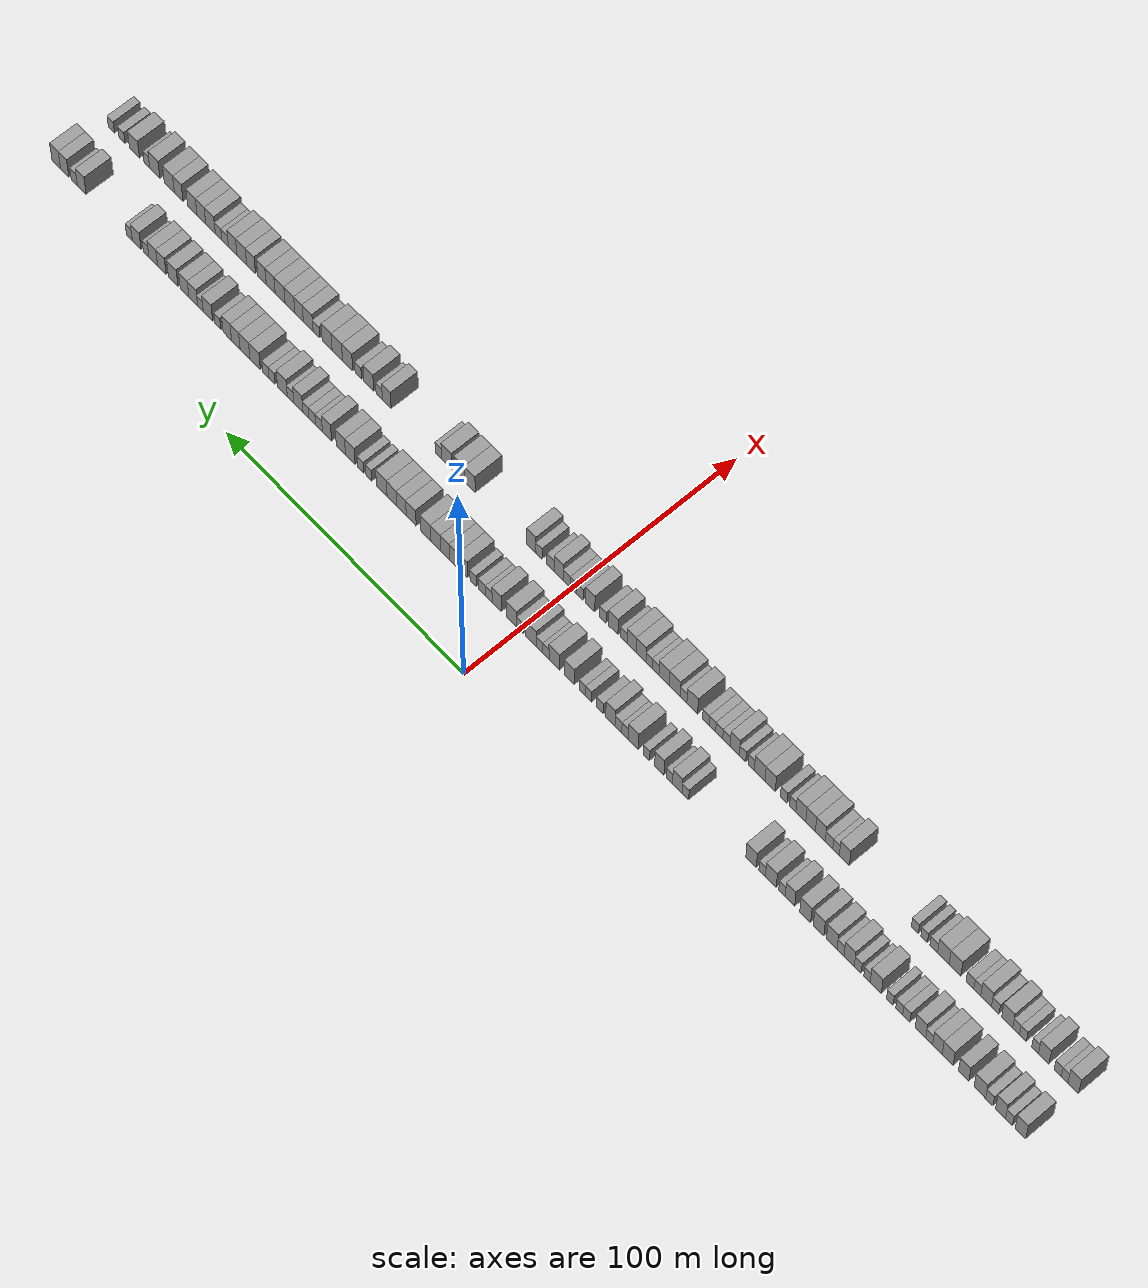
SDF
<sdf version="1.6">
 <world name="default">
  <scene>
   <sky><clouds><speed>12</speed></clouds></sky>
   <ambient>0.4 0.4 0.4 1</ambient>
   <background>0.7 0.7 0.7 1</background>
   <shadows>1</shadows>
  </scene>
  <gravity>0 0 -9.8066</gravity>
  <magnetic_field>6e-06 2.3e-05 -4.2e-05</magnetic_field>
  <physics default="0" name="default_physics" type="ode">
   <ode>
    <solver>
     <type>quick</type>
     <iters>10</iters>
     <sor>1.0</sor>
     <use_dynamic_moi_rescaling>0</use_dynamic_moi_rescaling>
    </solver>
    <constraints>
     <cfm>0</cfm>
     <erp>0.2</erp>
     <contact_max_correcting_vel>100</contact_max_correcting_vel>
     <contact_surface_layer>0.001</contact_surface_layer>
    </constraints>
   </ode>
   <max_step_size>0.004</max_step_size>
   <real_time_factor>1</real_time_factor>
   <real_time_update_rate>250</real_time_update_rate>
  </physics>
  <light name="sun" type="directional">
   <pose>0 0 10 0 0 0</pose>
   <diffuse>0.8 0.8 0.8 1</diffuse>
   <specular>0.2 0.2 0.2 1</specular>
   <attenuation>
    <range>1000</range>
    <constant>0.9</constant>
    <linear>0.01</linear>
    <quadratic>0.001</quadratic>
   </attenuation>
   <direction>-0.5 0.1 -0.9</direction>
  </light>
  <model name="building_1">
   <static>1</static>
   <pose>25.0000 -196.0010 0 0.000000 0.000000 0.000000</pose>
   <link name="link">
    <pose>0 0 4.50 0 0 0</pose>
    <collision name="collision"><geometry><box><size>10.0000 3.9981 9.0000</size></box></geometry></collision>
    <visual name="visual">
     <cast_shadows>0</cast_shadows>
     <geometry><box><size>10.0000 3.9981 9.0000</size></box></geometry>
     <material>
      <script>
       <uri>model://grey_wall/materials/scripts</uri>
       <uri>model://grey_wall/materials/textures</uri>
       <name>vrc/grey_wall</name>
      </script>
     </material>
    </visual>
   </link>
  </model>
  <model name="building_2">
   <static>1</static>
   <pose>25.0000 -191.7046 0 0.000000 0.000000 0.000000</pose>
   <link name="link">
    <pose>0 0 3.00 0 0 0</pose>
    <collision name="collision"><geometry><box><size>10.0000 2.5947 6.0000</size></box></geometry></collision>
    <visual name="visual">
     <cast_shadows>0</cast_shadows>
     <geometry><box><size>10.0000 2.5947 6.0000</size></box></geometry>
     <material>
      <script>
       <uri>model://grey_wall/materials/scripts</uri>
       <uri>model://grey_wall/materials/textures</uri>
       <name>vrc/grey_wall</name>
      </script>
     </material>
    </visual>
   </link>
  </model>
  <model name="building_3">
   <static>1</static>
   <pose>25.0000 -188.5552 0 0.000000 0.000000 0.000000</pose>
   <link name="link">
    <pose>0 0 4.50 0 0 0</pose>
    <collision name="collision"><geometry><box><size>10.0000 3.7041 9.0000</size></box></geometry></collision>
    <visual name="visual">
     <cast_shadows>0</cast_shadows>
     <geometry><box><size>10.0000 3.7041 9.0000</size></box></geometry>
     <material>
      <script>
       <uri>model://grey_wall/materials/scripts</uri>
       <uri>model://grey_wall/materials/textures</uri>
       <name>vrc/grey_wall</name>
      </script>
     </material>
    </visual>
   </link>
  </model>
  <model name="building_4">
   <static>1</static>
   <pose>25.0000 -184.3103 0 0.000000 0.000000 0.000000</pose>
   <link name="link">
    <pose>0 0 3.00 0 0 0</pose>
    <collision name="collision"><geometry><box><size>10.0000 2.7857 6.0000</size></box></geometry></collision>
    <visual name="visual">
     <cast_shadows>0</cast_shadows>
     <geometry><box><size>10.0000 2.7857 6.0000</size></box></geometry>
     <material>
      <script>
       <uri>model://grey_wall/materials/scripts</uri>
       <uri>model://grey_wall/materials/textures</uri>
       <name>vrc/grey_wall</name>
      </script>
     </material>
    </visual>
   </link>
  </model>
  <model name="building_5">
   <static>1</static>
   <pose>25.0000 -180.7664 0 0.000000 0.000000 0.000000</pose>
   <link name="link">
    <pose>0 0 4.50 0 0 0</pose>
    <collision name="collision"><geometry><box><size>10.0000 4.3021 9.0000</size></box></geometry></collision>
    <visual name="visual">
     <cast_shadows>0</cast_shadows>
     <geometry><box><size>10.0000 4.3021 9.0000</size></box></geometry>
     <material>
      <script>
       <uri>model://grey_wall/materials/scripts</uri>
       <uri>model://grey_wall/materials/textures</uri>
       <name>vrc/grey_wall</name>
      </script>
     </material>
    </visual>
   </link>
  </model>
  <model name="building_6">
   <static>1</static>
   <pose>25.0000 -174.6644 0 0.000000 0.000000 0.000000</pose>
   <link name="link">
    <pose>0 0 4.50 0 0 0</pose>
    <collision name="collision"><geometry><box><size>10.0000 3.9019 9.0000</size></box></geometry></collision>
    <visual name="visual">
     <cast_shadows>0</cast_shadows>
     <geometry><box><size>10.0000 3.9019 9.0000</size></box></geometry>
     <material>
      <script>
       <uri>model://grey_wall/materials/scripts</uri>
       <uri>model://grey_wall/materials/textures</uri>
       <name>vrc/grey_wall</name>
      </script>
     </material>
    </visual>
   </link>
  </model>
  <model name="building_7">
   <static>1</static>
   <pose>25.0000 -168.6367 0 0.000000 0.000000 0.000000</pose>
   <link name="link">
    <pose>0 0 4.50 0 0 0</pose>
    <collision name="collision"><geometry><box><size>10.0000 4.1534 9.0000</size></box></geometry></collision>
    <visual name="visual">
     <cast_shadows>0</cast_shadows>
     <geometry><box><size>10.0000 4.1534 9.0000</size></box></geometry>
     <material>
      <script>
       <uri>model://grey_wall/materials/scripts</uri>
       <uri>model://grey_wall/materials/textures</uri>
       <name>vrc/grey_wall</name>
      </script>
     </material>
    </visual>
   </link>
  </model>
  <model name="building_8">
   <static>1</static>
   <pose>25.0000 -164.7444 0 0.000000 0.000000 0.000000</pose>
   <link name="link">
    <pose>0 0 4.50 0 0 0</pose>
    <collision name="collision"><geometry><box><size>10.0000 3.6313 9.0000</size></box></geometry></collision>
    <visual name="visual">
     <cast_shadows>0</cast_shadows>
     <geometry><box><size>10.0000 3.6313 9.0000</size></box></geometry>
     <material>
      <script>
       <uri>model://grey_wall/materials/scripts</uri>
       <uri>model://grey_wall/materials/textures</uri>
       <name>vrc/grey_wall</name>
      </script>
     </material>
    </visual>
   </link>
  </model>
  <model name="building_9">
   <static>1</static>
   <pose>25.0000 -161.6257 0 0.000000 0.000000 0.000000</pose>
   <link name="link">
    <pose>0 0 3.00 0 0 0</pose>
    <collision name="collision"><geometry><box><size>10.0000 2.6060 6.0000</size></box></geometry></collision>
    <visual name="visual">
     <cast_shadows>0</cast_shadows>
     <geometry><box><size>10.0000 2.6060 6.0000</size></box></geometry>
     <material>
      <script>
       <uri>model://grey_wall/materials/scripts</uri>
       <uri>model://grey_wall/materials/textures</uri>
       <name>vrc/grey_wall</name>
      </script>
     </material>
    </visual>
   </link>
  </model>
  <model name="building_10">
   <static>1</static>
   <pose>25.0000 -158.3308 0 0.000000 0.000000 0.000000</pose>
   <link name="link">
    <pose>0 0 4.50 0 0 0</pose>
    <collision name="collision"><geometry><box><size>10.0000 3.9839 9.0000</size></box></geometry></collision>
    <visual name="visual">
     <cast_shadows>0</cast_shadows>
     <geometry><box><size>10.0000 3.9839 9.0000</size></box></geometry>
     <material>
      <script>
       <uri>model://grey_wall/materials/scripts</uri>
       <uri>model://grey_wall/materials/textures</uri>
       <name>vrc/grey_wall</name>
      </script>
     </material>
    </visual>
   </link>
  </model>
  <model name="building_11">
   <static>1</static>
   <pose>25.0000 -152.9566 0 0.000000 0.000000 0.000000</pose>
   <link name="link">
    <pose>0 0 3.00 0 0 0</pose>
    <collision name="collision"><geometry><box><size>10.0000 2.7644 6.0000</size></box></geometry></collision>
    <visual name="visual">
     <cast_shadows>0</cast_shadows>
     <geometry><box><size>10.0000 2.7644 6.0000</size></box></geometry>
     <material>
      <script>
       <uri>model://grey_wall/materials/scripts</uri>
       <uri>model://grey_wall/materials/textures</uri>
       <name>vrc/grey_wall</name>
      </script>
     </material>
    </visual>
   </link>
  </model>
  <model name="building_12">
   <static>1</static>
   <pose>25.0000 -150.2412 0 0.000000 0.000000 0.000000</pose>
   <link name="link">
    <pose>0 0 3.00 0 0 0</pose>
    <collision name="collision"><geometry><box><size>10.0000 2.6664 6.0000</size></box></geometry></collision>
    <visual name="visual">
     <cast_shadows>0</cast_shadows>
     <geometry><box><size>10.0000 2.6664 6.0000</size></box></geometry>
     <material>
      <script>
       <uri>model://grey_wall/materials/scripts</uri>
       <uri>model://grey_wall/materials/textures</uri>
       <name>vrc/grey_wall</name>
      </script>
     </material>
    </visual>
   </link>
  </model>
  <model name="building_13">
   <static>1</static>
   <pose>25.0000 -146.6483 0 0.000000 0.000000 0.000000</pose>
   <link name="link">
    <pose>0 0 3.00 0 0 0</pose>
    <collision name="collision"><geometry><box><size>10.0000 2.5195 6.0000</size></box></geometry></collision>
    <visual name="visual">
     <cast_shadows>0</cast_shadows>
     <geometry><box><size>10.0000 2.5195 6.0000</size></box></geometry>
     <material>
      <script>
       <uri>model://grey_wall/materials/scripts</uri>
       <uri>model://grey_wall/materials/textures</uri>
       <name>vrc/grey_wall</name>
      </script>
     </material>
    </visual>
   </link>
  </model>
  <model name="building_14">
   <static>1</static>
   <pose>25.0000 -141.2644 0 0.000000 0.000000 0.000000</pose>
   <link name="link">
    <pose>0 0 4.50 0 0 0</pose>
    <collision name="collision"><geometry><box><size>10.0000 4.2483 9.0000</size></box></geometry></collision>
    <visual name="visual">
     <cast_shadows>0</cast_shadows>
     <geometry><box><size>10.0000 4.2483 9.0000</size></box></geometry>
     <material>
      <script>
       <uri>model://grey_wall/materials/scripts</uri>
       <uri>model://grey_wall/materials/textures</uri>
       <name>vrc/grey_wall</name>
      </script>
     </material>
    </visual>
   </link>
  </model>
  <model name="building_15">
   <static>1</static>
   <pose>25.0000 -137.9141 0 0.000000 0.000000 0.000000</pose>
   <link name="link">
    <pose>0 0 3.00 0 0 0</pose>
    <collision name="collision"><geometry><box><size>10.0000 2.4524 6.0000</size></box></geometry></collision>
    <visual name="visual">
     <cast_shadows>0</cast_shadows>
     <geometry><box><size>10.0000 2.4524 6.0000</size></box></geometry>
     <material>
      <script>
       <uri>model://grey_wall/materials/scripts</uri>
       <uri>model://grey_wall/materials/textures</uri>
       <name>vrc/grey_wall</name>
      </script>
     </material>
    </visual>
   </link>
  </model>
  <model name="building_16">
   <static>1</static>
   <pose>25.0000 -134.3495 0 0.000000 0.000000 0.000000</pose>
   <link name="link">
    <pose>0 0 3.00 0 0 0</pose>
    <collision name="collision"><geometry><box><size>10.0000 2.6767 6.0000</size></box></geometry></collision>
    <visual name="visual">
     <cast_shadows>0</cast_shadows>
     <geometry><box><size>10.0000 2.6767 6.0000</size></box></geometry>
     <material>
      <script>
       <uri>model://grey_wall/materials/scripts</uri>
       <uri>model://grey_wall/materials/textures</uri>
       <name>vrc/grey_wall</name>
      </script>
     </material>
    </visual>
   </link>
  </model>
  <model name="building_17">
   <static>1</static>
   <pose>25.0000 -131.0443 0 0.000000 0.000000 0.000000</pose>
   <link name="link">
    <pose>0 0 4.50 0 0 0</pose>
    <collision name="collision"><geometry><box><size>10.0000 3.9338 9.0000</size></box></geometry></collision>
    <visual name="visual">
     <cast_shadows>0</cast_shadows>
     <geometry><box><size>10.0000 3.9338 9.0000</size></box></geometry>
     <material>
      <script>
       <uri>model://grey_wall/materials/scripts</uri>
       <uri>model://grey_wall/materials/textures</uri>
       <name>vrc/grey_wall</name>
      </script>
     </material>
    </visual>
   </link>
  </model>
  <model name="building_18">
   <static>1</static>
   <pose>25.0000 -127.7268 0 0.000000 0.000000 0.000000</pose>
   <link name="link">
    <pose>0 0 3.00 0 0 0</pose>
    <collision name="collision"><geometry><box><size>10.0000 2.7011 6.0000</size></box></geometry></collision>
    <visual name="visual">
     <cast_shadows>0</cast_shadows>
     <geometry><box><size>10.0000 2.7011 6.0000</size></box></geometry>
     <material>
      <script>
       <uri>model://grey_wall/materials/scripts</uri>
       <uri>model://grey_wall/materials/textures</uri>
       <name>vrc/grey_wall</name>
      </script>
     </material>
    </visual>
   </link>
  </model>
  <model name="building_19">
   <static>1</static>
   <pose>25.0000 -124.3317 0 0.000000 0.000000 0.000000</pose>
   <link name="link">
    <pose>0 0 4.50 0 0 0</pose>
    <collision name="collision"><geometry><box><size>10.0000 4.0892 9.0000</size></box></geometry></collision>
    <visual name="visual">
     <cast_shadows>0</cast_shadows>
     <geometry><box><size>10.0000 4.0892 9.0000</size></box></geometry>
     <material>
      <script>
       <uri>model://grey_wall/materials/scripts</uri>
       <uri>model://grey_wall/materials/textures</uri>
       <name>vrc/grey_wall</name>
      </script>
     </material>
    </visual>
   </link>
  </model>
  <model name="building_20">
   <static>1</static>
   <pose>25.0000 -119.2426 0 0.000000 0.000000 0.000000</pose>
   <link name="link">
    <pose>0 0 4.50 0 0 0</pose>
    <collision name="collision"><geometry><box><size>10.0000 4.0890 9.0000</size></box></geometry></collision>
    <visual name="visual">
     <cast_shadows>0</cast_shadows>
     <geometry><box><size>10.0000 4.0890 9.0000</size></box></geometry>
     <material>
      <script>
       <uri>model://grey_wall/materials/scripts</uri>
       <uri>model://grey_wall/materials/textures</uri>
       <name>vrc/grey_wall</name>
      </script>
     </material>
    </visual>
   </link>
  </model>
  <model name="building_21">
   <static>1</static>
   <pose>25.0000 -114.0799 0 0.000000 0.000000 0.000000</pose>
   <link name="link">
    <pose>0 0 4.50 0 0 0</pose>
    <collision name="collision"><geometry><box><size>10.0000 4.2363 9.0000</size></box></geometry></collision>
    <visual name="visual">
     <cast_shadows>0</cast_shadows>
     <geometry><box><size>10.0000 4.2363 9.0000</size></box></geometry>
     <material>
      <script>
       <uri>model://grey_wall/materials/scripts</uri>
       <uri>model://grey_wall/materials/textures</uri>
       <name>vrc/grey_wall</name>
      </script>
     </material>
    </visual>
   </link>
  </model>
  <model name="building_22">
   <static>1</static>
   <pose>25.0000 -108.1182 0 0.000000 0.000000 0.000000</pose>
   <link name="link">
    <pose>0 0 4.50 0 0 0</pose>
    <collision name="collision"><geometry><box><size>10.0000 3.6871 9.0000</size></box></geometry></collision>
    <visual name="visual">
     <cast_shadows>0</cast_shadows>
     <geometry><box><size>10.0000 3.6871 9.0000</size></box></geometry>
     <material>
      <script>
       <uri>model://grey_wall/materials/scripts</uri>
       <uri>model://grey_wall/materials/textures</uri>
       <name>vrc/grey_wall</name>
      </script>
     </material>
    </visual>
   </link>
  </model>
  <model name="building_23">
   <static>1</static>
   <pose>25.0000 -105.0206 0 0.000000 0.000000 0.000000</pose>
   <link name="link">
    <pose>0 0 3.00 0 0 0</pose>
    <collision name="collision"><geometry><box><size>10.0000 2.5081 6.0000</size></box></geometry></collision>
    <visual name="visual">
     <cast_shadows>0</cast_shadows>
     <geometry><box><size>10.0000 2.5081 6.0000</size></box></geometry>
     <material>
      <script>
       <uri>model://grey_wall/materials/scripts</uri>
       <uri>model://grey_wall/materials/textures</uri>
       <name>vrc/grey_wall</name>
      </script>
     </material>
    </visual>
   </link>
  </model>
  <model name="building_24">
   <static>1</static>
   <pose>25.0000 -100.6640 0 0.000000 0.000000 0.000000</pose>
   <link name="link">
    <pose>0 0 4.50 0 0 0</pose>
    <collision name="collision"><geometry><box><size>10.0000 4.2052 9.0000</size></box></geometry></collision>
    <visual name="visual">
     <cast_shadows>0</cast_shadows>
     <geometry><box><size>10.0000 4.2052 9.0000</size></box></geometry>
     <material>
      <script>
       <uri>model://grey_wall/materials/scripts</uri>
       <uri>model://grey_wall/materials/textures</uri>
       <name>vrc/grey_wall</name>
      </script>
     </material>
    </visual>
   </link>
  </model>
  <model name="building_25">
   <static>1</static>
   <pose>25.0000 -97.2707 0 0.000000 0.000000 0.000000</pose>
   <link name="link">
    <pose>0 0 3.00 0 0 0</pose>
    <collision name="collision"><geometry><box><size>10.0000 2.5814 6.0000</size></box></geometry></collision>
    <visual name="visual">
     <cast_shadows>0</cast_shadows>
     <geometry><box><size>10.0000 2.5814 6.0000</size></box></geometry>
     <material>
      <script>
       <uri>model://grey_wall/materials/scripts</uri>
       <uri>model://grey_wall/materials/textures</uri>
       <name>vrc/grey_wall</name>
      </script>
     </material>
    </visual>
   </link>
  </model>
  <model name="building_26">
   <static>1</static>
   <pose>25.0000 -92.9338 0 0.000000 0.000000 0.000000</pose>
   <link name="link">
    <pose>0 0 4.50 0 0 0</pose>
    <collision name="collision"><geometry><box><size>10.0000 4.0925 9.0000</size></box></geometry></collision>
    <visual name="visual">
     <cast_shadows>0</cast_shadows>
     <geometry><box><size>10.0000 4.0925 9.0000</size></box></geometry>
     <material>
      <script>
       <uri>model://grey_wall/materials/scripts</uri>
       <uri>model://grey_wall/materials/textures</uri>
       <name>vrc/grey_wall</name>
      </script>
     </material>
    </visual>
   </link>
  </model>
  <model name="building_27">
   <static>1</static>
   <pose>25.0000 -67.0215 0 0.000000 0.000000 0.000000</pose>
   <link name="link">
    <pose>0 0 3.00 0 0 0</pose>
    <collision name="collision"><geometry><box><size>10.0000 2.5773 6.0000</size></box></geometry></collision>
    <visual name="visual">
     <cast_shadows>0</cast_shadows>
     <geometry><box><size>10.0000 2.5773 6.0000</size></box></geometry>
     <material>
      <script>
       <uri>model://grey_wall/materials/scripts</uri>
       <uri>model://grey_wall/materials/textures</uri>
       <name>vrc/grey_wall</name>
      </script>
     </material>
    </visual>
   </link>
  </model>
  <model name="building_28">
   <static>1</static>
   <pose>25.0000 -63.8202 0 0.000000 0.000000 0.000000</pose>
   <link name="link">
    <pose>0 0 4.50 0 0 0</pose>
    <collision name="collision"><geometry><box><size>10.0000 3.8253 9.0000</size></box></geometry></collision>
    <visual name="visual">
     <cast_shadows>0</cast_shadows>
     <geometry><box><size>10.0000 3.8253 9.0000</size></box></geometry>
     <material>
      <script>
       <uri>model://grey_wall/materials/scripts</uri>
       <uri>model://grey_wall/materials/textures</uri>
       <name>vrc/grey_wall</name>
      </script>
     </material>
    </visual>
   </link>
  </model>
  <model name="building_29">
   <static>1</static>
   <pose>25.0000 -60.6753 0 0.000000 0.000000 0.000000</pose>
   <link name="link">
    <pose>0 0 3.00 0 0 0</pose>
    <collision name="collision"><geometry><box><size>10.0000 2.4644 6.0000</size></box></geometry></collision>
    <visual name="visual">
     <cast_shadows>0</cast_shadows>
     <geometry><box><size>10.0000 2.4644 6.0000</size></box></geometry>
     <material>
      <script>
       <uri>model://grey_wall/materials/scripts</uri>
       <uri>model://grey_wall/materials/textures</uri>
       <name>vrc/grey_wall</name>
      </script>
     </material>
    </visual>
   </link>
  </model>
  <model name="building_30">
   <static>1</static>
   <pose>25.0000 -56.6034 0 0.000000 0.000000 0.000000</pose>
   <link name="link">
    <pose>0 0 4.50 0 0 0</pose>
    <collision name="collision"><geometry><box><size>10.0000 3.6793 9.0000</size></box></geometry></collision>
    <visual name="visual">
     <cast_shadows>0</cast_shadows>
     <geometry><box><size>10.0000 3.6793 9.0000</size></box></geometry>
     <material>
      <script>
       <uri>model://grey_wall/materials/scripts</uri>
       <uri>model://grey_wall/materials/textures</uri>
       <name>vrc/grey_wall</name>
      </script>
     </material>
    </visual>
   </link>
  </model>
  <model name="building_31">
   <static>1</static>
   <pose>25.0000 -51.5045 0 0.000000 0.000000 0.000000</pose>
   <link name="link">
    <pose>0 0 3.00 0 0 0</pose>
    <collision name="collision"><geometry><box><size>10.0000 2.5185 6.0000</size></box></geometry></collision>
    <visual name="visual">
     <cast_shadows>0</cast_shadows>
     <geometry><box><size>10.0000 2.5185 6.0000</size></box></geometry>
     <material>
      <script>
       <uri>model://grey_wall/materials/scripts</uri>
       <uri>model://grey_wall/materials/textures</uri>
       <name>vrc/grey_wall</name>
      </script>
     </material>
    </visual>
   </link>
  </model>
  <model name="building_32">
   <static>1</static>
   <pose>25.0000 -46.1726 0 0.000000 0.000000 0.000000</pose>
   <link name="link">
    <pose>0 0 4.50 0 0 0</pose>
    <collision name="collision"><geometry><box><size>10.0000 4.1452 9.0000</size></box></geometry></collision>
    <visual name="visual">
     <cast_shadows>0</cast_shadows>
     <geometry><box><size>10.0000 4.1452 9.0000</size></box></geometry>
     <material>
      <script>
       <uri>model://grey_wall/materials/scripts</uri>
       <uri>model://grey_wall/materials/textures</uri>
       <name>vrc/grey_wall</name>
      </script>
     </material>
    </visual>
   </link>
  </model>
  <model name="building_33">
   <static>1</static>
   <pose>25.0000 -42.8360 0 0.000000 0.000000 0.000000</pose>
   <link name="link">
    <pose>0 0 3.00 0 0 0</pose>
    <collision name="collision"><geometry><box><size>10.0000 2.5281 6.0000</size></box></geometry></collision>
    <visual name="visual">
     <cast_shadows>0</cast_shadows>
     <geometry><box><size>10.0000 2.5281 6.0000</size></box></geometry>
     <material>
      <script>
       <uri>model://grey_wall/materials/scripts</uri>
       <uri>model://grey_wall/materials/textures</uri>
       <name>vrc/grey_wall</name>
      </script>
     </material>
    </visual>
   </link>
  </model>
  <model name="building_34">
   <static>1</static>
   <pose>25.0000 -40.1907 0 0.000000 0.000000 0.000000</pose>
   <link name="link">
    <pose>0 0 3.00 0 0 0</pose>
    <collision name="collision"><geometry><box><size>10.0000 2.7624 6.0000</size></box></geometry></collision>
    <visual name="visual">
     <cast_shadows>0</cast_shadows>
     <geometry><box><size>10.0000 2.7624 6.0000</size></box></geometry>
     <material>
      <script>
       <uri>model://grey_wall/materials/scripts</uri>
       <uri>model://grey_wall/materials/textures</uri>
       <name>vrc/grey_wall</name>
      </script>
     </material>
    </visual>
   </link>
  </model>
  <model name="building_35">
   <static>1</static>
   <pose>25.0000 -36.9668 0 0.000000 0.000000 0.000000</pose>
   <link name="link">
    <pose>0 0 4.50 0 0 0</pose>
    <collision name="collision"><geometry><box><size>10.0000 3.6854 9.0000</size></box></geometry></collision>
    <visual name="visual">
     <cast_shadows>0</cast_shadows>
     <geometry><box><size>10.0000 3.6854 9.0000</size></box></geometry>
     <material>
      <script>
       <uri>model://grey_wall/materials/scripts</uri>
       <uri>model://grey_wall/materials/textures</uri>
       <name>vrc/grey_wall</name>
      </script>
     </material>
    </visual>
   </link>
  </model>
  <model name="building_36">
   <static>1</static>
   <pose>25.0000 -32.7371 0 0.000000 0.000000 0.000000</pose>
   <link name="link">
    <pose>0 0 3.00 0 0 0</pose>
    <collision name="collision"><geometry><box><size>10.0000 2.7739 6.0000</size></box></geometry></collision>
    <visual name="visual">
     <cast_shadows>0</cast_shadows>
     <geometry><box><size>10.0000 2.7739 6.0000</size></box></geometry>
     <material>
      <script>
       <uri>model://grey_wall/materials/scripts</uri>
       <uri>model://grey_wall/materials/textures</uri>
       <name>vrc/grey_wall</name>
      </script>
     </material>
    </visual>
   </link>
  </model>
  <model name="building_37">
   <static>1</static>
   <pose>25.0000 -28.1417 0 0.000000 0.000000 0.000000</pose>
   <link name="link">
    <pose>0 0 3.00 0 0 0</pose>
    <collision name="collision"><geometry><box><size>10.0000 2.4168 6.0000</size></box></geometry></collision>
    <visual name="visual">
     <cast_shadows>0</cast_shadows>
     <geometry><box><size>10.0000 2.4168 6.0000</size></box></geometry>
     <material>
      <script>
       <uri>model://grey_wall/materials/scripts</uri>
       <uri>model://grey_wall/materials/textures</uri>
       <name>vrc/grey_wall</name>
      </script>
     </material>
    </visual>
   </link>
  </model>
  <model name="building_38">
   <static>1</static>
   <pose>25.0000 -25.6398 0 0.000000 0.000000 0.000000</pose>
   <link name="link">
    <pose>0 0 3.00 0 0 0</pose>
    <collision name="collision"><geometry><box><size>10.0000 2.5871 6.0000</size></box></geometry></collision>
    <visual name="visual">
     <cast_shadows>0</cast_shadows>
     <geometry><box><size>10.0000 2.5871 6.0000</size></box></geometry>
     <material>
      <script>
       <uri>model://grey_wall/materials/scripts</uri>
       <uri>model://grey_wall/materials/textures</uri>
       <name>vrc/grey_wall</name>
      </script>
     </material>
    </visual>
   </link>
  </model>
  <model name="building_39">
   <static>1</static>
   <pose>25.0000 -20.3670 0 0.000000 0.000000 0.000000</pose>
   <link name="link">
    <pose>0 0 4.50 0 0 0</pose>
    <collision name="collision"><geometry><box><size>10.0000 3.9584 9.0000</size></box></geometry></collision>
    <visual name="visual">
     <cast_shadows>0</cast_shadows>
     <geometry><box><size>10.0000 3.9584 9.0000</size></box></geometry>
     <material>
      <script>
       <uri>model://grey_wall/materials/scripts</uri>
       <uri>model://grey_wall/materials/textures</uri>
       <name>vrc/grey_wall</name>
      </script>
     </material>
    </visual>
   </link>
  </model>
  <model name="building_40">
   <static>1</static>
   <pose>25.0000 -14.2242 0 0.000000 0.000000 0.000000</pose>
   <link name="link">
    <pose>0 0 4.50 0 0 0</pose>
    <collision name="collision"><geometry><box><size>10.0000 4.3272 9.0000</size></box></geometry></collision>
    <visual name="visual">
     <cast_shadows>0</cast_shadows>
     <geometry><box><size>10.0000 4.3272 9.0000</size></box></geometry>
     <material>
      <script>
       <uri>model://grey_wall/materials/scripts</uri>
       <uri>model://grey_wall/materials/textures</uri>
       <name>vrc/grey_wall</name>
      </script>
     </material>
    </visual>
   </link>
  </model>
  <model name="building_41">
   <static>1</static>
   <pose>25.0000 -10.8219 0 0.000000 0.000000 0.000000</pose>
   <link name="link">
    <pose>0 0 3.00 0 0 0</pose>
    <collision name="collision"><geometry><box><size>10.0000 2.4773 6.0000</size></box></geometry></collision>
    <visual name="visual">
     <cast_shadows>0</cast_shadows>
     <geometry><box><size>10.0000 2.4773 6.0000</size></box></geometry>
     <material>
      <script>
       <uri>model://grey_wall/materials/scripts</uri>
       <uri>model://grey_wall/materials/textures</uri>
       <name>vrc/grey_wall</name>
      </script>
     </material>
    </visual>
   </link>
  </model>
  <model name="building_42">
   <static>1</static>
   <pose>25.0000 -8.2624 0 0.000000 0.000000 0.000000</pose>
   <link name="link">
    <pose>0 0 3.00 0 0 0</pose>
    <collision name="collision"><geometry><box><size>10.0000 2.6418 6.0000</size></box></geometry></collision>
    <visual name="visual">
     <cast_shadows>0</cast_shadows>
     <geometry><box><size>10.0000 2.6418 6.0000</size></box></geometry>
     <material>
      <script>
       <uri>model://grey_wall/materials/scripts</uri>
       <uri>model://grey_wall/materials/textures</uri>
       <name>vrc/grey_wall</name>
      </script>
     </material>
    </visual>
   </link>
  </model>
  <model name="building_43">
   <static>1</static>
   <pose>25.0000 -4.7868 0 0.000000 0.000000 0.000000</pose>
   <link name="link">
    <pose>0 0 4.50 0 0 0</pose>
    <collision name="collision"><geometry><box><size>10.0000 4.3095 9.0000</size></box></geometry></collision>
    <visual name="visual">
     <cast_shadows>0</cast_shadows>
     <geometry><box><size>10.0000 4.3095 9.0000</size></box></geometry>
     <material>
      <script>
       <uri>model://grey_wall/materials/scripts</uri>
       <uri>model://grey_wall/materials/textures</uri>
       <name>vrc/grey_wall</name>
      </script>
     </material>
    </visual>
   </link>
  </model>
  <model name="building_44">
   <static>1</static>
   <pose>25.0000 -0.2851 0 0.000000 0.000000 0.000000</pose>
   <link name="link">
    <pose>0 0 3.00 0 0 0</pose>
    <collision name="collision"><geometry><box><size>10.0000 2.6940 6.0000</size></box></geometry></collision>
    <visual name="visual">
     <cast_shadows>0</cast_shadows>
     <geometry><box><size>10.0000 2.6940 6.0000</size></box></geometry>
     <material>
      <script>
       <uri>model://grey_wall/materials/scripts</uri>
       <uri>model://grey_wall/materials/textures</uri>
       <name>vrc/grey_wall</name>
      </script>
     </material>
    </visual>
   </link>
  </model>
  <model name="building_45">
   <static>1</static>
   <pose>25.0000 3.2484 0 0.000000 0.000000 0.000000</pose>
   <link name="link">
    <pose>0 0 4.50 0 0 0</pose>
    <collision name="collision"><geometry><box><size>10.0000 4.3729 9.0000</size></box></geometry></collision>
    <visual name="visual">
     <cast_shadows>0</cast_shadows>
     <geometry><box><size>10.0000 4.3729 9.0000</size></box></geometry>
     <material>
      <script>
       <uri>model://grey_wall/materials/scripts</uri>
       <uri>model://grey_wall/materials/textures</uri>
       <name>vrc/grey_wall</name>
      </script>
     </material>
    </visual>
   </link>
  </model>
  <model name="building_46">
   <static>1</static>
   <pose>25.0000 9.3493 0 0.000000 0.000000 0.000000</pose>
   <link name="link">
    <pose>0 0 4.50 0 0 0</pose>
    <collision name="collision"><geometry><box><size>10.0000 3.8289 9.0000</size></box></geometry></collision>
    <visual name="visual">
     <cast_shadows>0</cast_shadows>
     <geometry><box><size>10.0000 3.8289 9.0000</size></box></geometry>
     <material>
      <script>
       <uri>model://grey_wall/materials/scripts</uri>
       <uri>model://grey_wall/materials/textures</uri>
       <name>vrc/grey_wall</name>
      </script>
     </material>
    </visual>
   </link>
  </model>
  <model name="building_47">
   <static>1</static>
   <pose>25.0000 12.5972 0 0.000000 0.000000 0.000000</pose>
   <link name="link">
    <pose>0 0 3.00 0 0 0</pose>
    <collision name="collision"><geometry><box><size>10.0000 2.6668 6.0000</size></box></geometry></collision>
    <visual name="visual">
     <cast_shadows>0</cast_shadows>
     <geometry><box><size>10.0000 2.6668 6.0000</size></box></geometry>
     <material>
      <script>
       <uri>model://grey_wall/materials/scripts</uri>
       <uri>model://grey_wall/materials/textures</uri>
       <name>vrc/grey_wall</name>
      </script>
     </material>
    </visual>
   </link>
  </model>
  <model name="building_48">
   <static>1</static>
   <pose>25.0000 15.3865 0 0.000000 0.000000 0.000000</pose>
   <link name="link">
    <pose>0 0 3.00 0 0 0</pose>
    <collision name="collision"><geometry><box><size>10.0000 2.9118 6.0000</size></box></geometry></collision>
    <visual name="visual">
     <cast_shadows>0</cast_shadows>
     <geometry><box><size>10.0000 2.9118 6.0000</size></box></geometry>
     <material>
      <script>
       <uri>model://grey_wall/materials/scripts</uri>
       <uri>model://grey_wall/materials/textures</uri>
       <name>vrc/grey_wall</name>
      </script>
     </material>
    </visual>
   </link>
  </model>
  <model name="building_49">
   <static>1</static>
   <pose>25.0000 19.1278 0 0.000000 0.000000 0.000000</pose>
   <link name="link">
    <pose>0 0 3.00 0 0 0</pose>
    <collision name="collision"><geometry><box><size>10.0000 2.5707 6.0000</size></box></geometry></collision>
    <visual name="visual">
     <cast_shadows>0</cast_shadows>
     <geometry><box><size>10.0000 2.5707 6.0000</size></box></geometry>
     <material>
      <script>
       <uri>model://grey_wall/materials/scripts</uri>
       <uri>model://grey_wall/materials/textures</uri>
       <name>vrc/grey_wall</name>
      </script>
     </material>
    </visual>
   </link>
  </model>
  <model name="building_50">
   <static>1</static>
   <pose>25.0000 23.2987 0 0.000000 0.000000 0.000000</pose>
   <link name="link">
    <pose>0 0 4.50 0 0 0</pose>
    <collision name="collision"><geometry><box><size>10.0000 3.7711 9.0000</size></box></geometry></collision>
    <visual name="visual">
     <cast_shadows>0</cast_shadows>
     <geometry><box><size>10.0000 3.7711 9.0000</size></box></geometry>
     <material>
      <script>
       <uri>model://grey_wall/materials/scripts</uri>
       <uri>model://grey_wall/materials/textures</uri>
       <name>vrc/grey_wall</name>
      </script>
     </material>
    </visual>
   </link>
  </model>
  <model name="building_51">
   <static>1</static>
   <pose>25.0000 27.0453 0 0.000000 0.000000 0.000000</pose>
   <link name="link">
    <pose>0 0 4.50 0 0 0</pose>
    <collision name="collision"><geometry><box><size>10.0000 3.7221 9.0000</size></box></geometry></collision>
    <visual name="visual">
     <cast_shadows>0</cast_shadows>
     <geometry><box><size>10.0000 3.7221 9.0000</size></box></geometry>
     <material>
      <script>
       <uri>model://grey_wall/materials/scripts</uri>
       <uri>model://grey_wall/materials/textures</uri>
       <name>vrc/grey_wall</name>
      </script>
     </material>
    </visual>
   </link>
  </model>
  <model name="building_52">
   <static>1</static>
   <pose>25.0000 30.7157 0 0.000000 0.000000 0.000000</pose>
   <link name="link">
    <pose>0 0 4.50 0 0 0</pose>
    <collision name="collision"><geometry><box><size>10.0000 3.6187 9.0000</size></box></geometry></collision>
    <visual name="visual">
     <cast_shadows>0</cast_shadows>
     <geometry><box><size>10.0000 3.6187 9.0000</size></box></geometry>
     <material>
      <script>
       <uri>model://grey_wall/materials/scripts</uri>
       <uri>model://grey_wall/materials/textures</uri>
       <name>vrc/grey_wall</name>
      </script>
     </material>
    </visual>
   </link>
  </model>
  <model name="building_53">
   <static>1</static>
   <pose>25.0000 34.5919 0 0.000000 0.000000 0.000000</pose>
   <link name="link">
    <pose>0 0 4.50 0 0 0</pose>
    <collision name="collision"><geometry><box><size>10.0000 4.1337 9.0000</size></box></geometry></collision>
    <visual name="visual">
     <cast_shadows>0</cast_shadows>
     <geometry><box><size>10.0000 4.1337 9.0000</size></box></geometry>
     <material>
      <script>
       <uri>model://grey_wall/materials/scripts</uri>
       <uri>model://grey_wall/materials/textures</uri>
       <name>vrc/grey_wall</name>
      </script>
     </material>
    </visual>
   </link>
  </model>
  <model name="building_54">
   <static>1</static>
   <pose>25.0000 38.7498 0 0.000000 0.000000 0.000000</pose>
   <link name="link">
    <pose>0 0 4.50 0 0 0</pose>
    <collision name="collision"><geometry><box><size>10.0000 4.1821 9.0000</size></box></geometry></collision>
    <visual name="visual">
     <cast_shadows>0</cast_shadows>
     <geometry><box><size>10.0000 4.1821 9.0000</size></box></geometry>
     <material>
      <script>
       <uri>model://grey_wall/materials/scripts</uri>
       <uri>model://grey_wall/materials/textures</uri>
       <name>vrc/grey_wall</name>
      </script>
     </material>
    </visual>
   </link>
  </model>
  <model name="building_55">
   <static>1</static>
   <pose>25.0000 44.9251 0 0.000000 0.000000 0.000000</pose>
   <link name="link">
    <pose>0 0 4.50 0 0 0</pose>
    <collision name="collision"><geometry><box><size>10.0000 4.1687 9.0000</size></box></geometry></collision>
    <visual name="visual">
     <cast_shadows>0</cast_shadows>
     <geometry><box><size>10.0000 4.1687 9.0000</size></box></geometry>
     <material>
      <script>
       <uri>model://grey_wall/materials/scripts</uri>
       <uri>model://grey_wall/materials/textures</uri>
       <name>vrc/grey_wall</name>
      </script>
     </material>
    </visual>
   </link>
  </model>
  <model name="building_56">
   <static>1</static>
   <pose>25.0000 48.9636 0 0.000000 0.000000 0.000000</pose>
   <link name="link">
    <pose>0 0 4.50 0 0 0</pose>
    <collision name="collision"><geometry><box><size>10.0000 3.9081 9.0000</size></box></geometry></collision>
    <visual name="visual">
     <cast_shadows>0</cast_shadows>
     <geometry><box><size>10.0000 3.9081 9.0000</size></box></geometry>
     <material>
      <script>
       <uri>model://grey_wall/materials/scripts</uri>
       <uri>model://grey_wall/materials/textures</uri>
       <name>vrc/grey_wall</name>
      </script>
     </material>
    </visual>
   </link>
  </model>
  <model name="building_57">
   <static>1</static>
   <pose>25.0000 52.9818 0 0.000000 0.000000 0.000000</pose>
   <link name="link">
    <pose>0 0 4.50 0 0 0</pose>
    <collision name="collision"><geometry><box><size>10.0000 4.1284 9.0000</size></box></geometry></collision>
    <visual name="visual">
     <cast_shadows>0</cast_shadows>
     <geometry><box><size>10.0000 4.1284 9.0000</size></box></geometry>
     <material>
      <script>
       <uri>model://grey_wall/materials/scripts</uri>
       <uri>model://grey_wall/materials/textures</uri>
       <name>vrc/grey_wall</name>
      </script>
     </material>
    </visual>
   </link>
  </model>
  <model name="building_58">
   <static>1</static>
   <pose>25.0000 57.2910 0 0.000000 0.000000 0.000000</pose>
   <link name="link">
    <pose>0 0 4.50 0 0 0</pose>
    <collision name="collision"><geometry><box><size>10.0000 4.4899 9.0000</size></box></geometry></collision>
    <visual name="visual">
     <cast_shadows>0</cast_shadows>
     <geometry><box><size>10.0000 4.4899 9.0000</size></box></geometry>
     <material>
      <script>
       <uri>model://grey_wall/materials/scripts</uri>
       <uri>model://grey_wall/materials/textures</uri>
       <name>vrc/grey_wall</name>
      </script>
     </material>
    </visual>
   </link>
  </model>
  <model name="building_59">
   <static>1</static>
   <pose>25.0000 62.7533 0 0.000000 0.000000 0.000000</pose>
   <link name="link">
    <pose>0 0 3.00 0 0 0</pose>
    <collision name="collision"><geometry><box><size>10.0000 2.4347 6.0000</size></box></geometry></collision>
    <visual name="visual">
     <cast_shadows>0</cast_shadows>
     <geometry><box><size>10.0000 2.4347 6.0000</size></box></geometry>
     <material>
      <script>
       <uri>model://grey_wall/materials/scripts</uri>
       <uri>model://grey_wall/materials/textures</uri>
       <name>vrc/grey_wall</name>
      </script>
     </material>
    </visual>
   </link>
  </model>
  <model name="building_60">
   <static>1</static>
   <pose>25.0000 66.2779 0 0.000000 0.000000 0.000000</pose>
   <link name="link">
    <pose>0 0 3.00 0 0 0</pose>
    <collision name="collision"><geometry><box><size>10.0000 2.6145 6.0000</size></box></geometry></collision>
    <visual name="visual">
     <cast_shadows>0</cast_shadows>
     <geometry><box><size>10.0000 2.6145 6.0000</size></box></geometry>
     <material>
      <script>
       <uri>model://grey_wall/materials/scripts</uri>
       <uri>model://grey_wall/materials/textures</uri>
       <name>vrc/grey_wall</name>
      </script>
     </material>
    </visual>
   </link>
  </model>
  <model name="building_61">
   <static>1</static>
   <pose>25.0000 70.6246 0 0.000000 0.000000 0.000000</pose>
   <link name="link">
    <pose>0 0 4.50 0 0 0</pose>
    <collision name="collision"><geometry><box><size>10.0000 4.0791 9.0000</size></box></geometry></collision>
    <visual name="visual">
     <cast_shadows>0</cast_shadows>
     <geometry><box><size>10.0000 4.0791 9.0000</size></box></geometry>
     <material>
      <script>
       <uri>model://grey_wall/materials/scripts</uri>
       <uri>model://grey_wall/materials/textures</uri>
       <name>vrc/grey_wall</name>
      </script>
     </material>
    </visual>
   </link>
  </model>
  <model name="building_62">
   <static>1</static>
   <pose>25.0000 74.6228 0 0.000000 0.000000 0.000000</pose>
   <link name="link">
    <pose>0 0 4.50 0 0 0</pose>
    <collision name="collision"><geometry><box><size>10.0000 3.9172 9.0000</size></box></geometry></collision>
    <visual name="visual">
     <cast_shadows>0</cast_shadows>
     <geometry><box><size>10.0000 3.9172 9.0000</size></box></geometry>
     <material>
      <script>
       <uri>model://grey_wall/materials/scripts</uri>
       <uri>model://grey_wall/materials/textures</uri>
       <name>vrc/grey_wall</name>
      </script>
     </material>
    </visual>
   </link>
  </model>
  <model name="building_63">
   <static>1</static>
   <pose>25.0000 80.5359 0 0.000000 0.000000 0.000000</pose>
   <link name="link">
    <pose>0 0 4.50 0 0 0</pose>
    <collision name="collision"><geometry><box><size>10.0000 3.9089 9.0000</size></box></geometry></collision>
    <visual name="visual">
     <cast_shadows>0</cast_shadows>
     <geometry><box><size>10.0000 3.9089 9.0000</size></box></geometry>
     <material>
      <script>
       <uri>model://grey_wall/materials/scripts</uri>
       <uri>model://grey_wall/materials/textures</uri>
       <name>vrc/grey_wall</name>
      </script>
     </material>
    </visual>
   </link>
  </model>
  <model name="building_64">
   <static>1</static>
   <pose>25.0000 83.9480 0 0.000000 0.000000 0.000000</pose>
   <link name="link">
    <pose>0 0 3.00 0 0 0</pose>
    <collision name="collision"><geometry><box><size>10.0000 2.9154 6.0000</size></box></geometry></collision>
    <visual name="visual">
     <cast_shadows>0</cast_shadows>
     <geometry><box><size>10.0000 2.9154 6.0000</size></box></geometry>
     <material>
      <script>
       <uri>model://grey_wall/materials/scripts</uri>
       <uri>model://grey_wall/materials/textures</uri>
       <name>vrc/grey_wall</name>
      </script>
     </material>
    </visual>
   </link>
  </model>
  <model name="building_65">
   <static>1</static>
   <pose>25.0000 86.8324 0 0.000000 0.000000 0.000000</pose>
   <link name="link">
    <pose>0 0 3.00 0 0 0</pose>
    <collision name="collision"><geometry><box><size>10.0000 2.8534 6.0000</size></box></geometry></collision>
    <visual name="visual">
     <cast_shadows>0</cast_shadows>
     <geometry><box><size>10.0000 2.8534 6.0000</size></box></geometry>
     <material>
      <script>
       <uri>model://grey_wall/materials/scripts</uri>
       <uri>model://grey_wall/materials/textures</uri>
       <name>vrc/grey_wall</name>
      </script>
     </material>
    </visual>
   </link>
  </model>
  <model name="building_66">
   <static>1</static>
   <pose>25.0000 89.5290 0 0.000000 0.000000 0.000000</pose>
   <link name="link">
    <pose>0 0 3.00 0 0 0</pose>
    <collision name="collision"><geometry><box><size>10.0000 2.5396 6.0000</size></box></geometry></collision>
    <visual name="visual">
     <cast_shadows>0</cast_shadows>
     <geometry><box><size>10.0000 2.5396 6.0000</size></box></geometry>
     <material>
      <script>
       <uri>model://grey_wall/materials/scripts</uri>
       <uri>model://grey_wall/materials/textures</uri>
       <name>vrc/grey_wall</name>
      </script>
     </material>
    </visual>
   </link>
  </model>
  <model name="building_67">
   <static>1</static>
   <pose>25.0000 92.7599 0 0.000000 0.000000 0.000000</pose>
   <link name="link">
    <pose>0 0 4.50 0 0 0</pose>
    <collision name="collision"><geometry><box><size>10.0000 3.9223 9.0000</size></box></geometry></collision>
    <visual name="visual">
     <cast_shadows>0</cast_shadows>
     <geometry><box><size>10.0000 3.9223 9.0000</size></box></geometry>
     <material>
      <script>
       <uri>model://grey_wall/materials/scripts</uri>
       <uri>model://grey_wall/materials/textures</uri>
       <name>vrc/grey_wall</name>
      </script>
     </material>
    </visual>
   </link>
  </model>
  <model name="building_68">
   <static>1</static>
   <pose>25.0000 96.1398 0 0.000000 0.000000 0.000000</pose>
   <link name="link">
    <pose>0 0 3.00 0 0 0</pose>
    <collision name="collision"><geometry><box><size>10.0000 2.8376 6.0000</size></box></geometry></collision>
    <visual name="visual">
     <cast_shadows>0</cast_shadows>
     <geometry><box><size>10.0000 2.8376 6.0000</size></box></geometry>
     <material>
      <script>
       <uri>model://grey_wall/materials/scripts</uri>
       <uri>model://grey_wall/materials/textures</uri>
       <name>vrc/grey_wall</name>
      </script>
     </material>
    </visual>
   </link>
  </model>
  <model name="building_69">
   <static>1</static>
   <pose>25.0000 99.6629 0 0.000000 0.000000 0.000000</pose>
   <link name="link">
    <pose>0 0 4.50 0 0 0</pose>
    <collision name="collision"><geometry><box><size>10.0000 4.2086 9.0000</size></box></geometry></collision>
    <visual name="visual">
     <cast_shadows>0</cast_shadows>
     <geometry><box><size>10.0000 4.2086 9.0000</size></box></geometry>
     <material>
      <script>
       <uri>model://grey_wall/materials/scripts</uri>
       <uri>model://grey_wall/materials/textures</uri>
       <name>vrc/grey_wall</name>
      </script>
     </material>
    </visual>
   </link>
  </model>
  <model name="building_70">
   <static>1</static>
   <pose>25.0000 104.0911 0 0.000000 0.000000 0.000000</pose>
   <link name="link">
    <pose>0 0 3.00 0 0 0</pose>
    <collision name="collision"><geometry><box><size>10.0000 2.6479 6.0000</size></box></geometry></collision>
    <visual name="visual">
     <cast_shadows>0</cast_shadows>
     <geometry><box><size>10.0000 2.6479 6.0000</size></box></geometry>
     <material>
      <script>
       <uri>model://grey_wall/materials/scripts</uri>
       <uri>model://grey_wall/materials/textures</uri>
       <name>vrc/grey_wall</name>
      </script>
     </material>
    </visual>
   </link>
  </model>
  <model name="building_71">
   <static>1</static>
   <pose>25.0000 106.7862 0 0.000000 0.000000 0.000000</pose>
   <link name="link">
    <pose>0 0 3.00 0 0 0</pose>
    <collision name="collision"><geometry><box><size>10.0000 2.7424 6.0000</size></box></geometry></collision>
    <visual name="visual">
     <cast_shadows>0</cast_shadows>
     <geometry><box><size>10.0000 2.7424 6.0000</size></box></geometry>
     <material>
      <script>
       <uri>model://grey_wall/materials/scripts</uri>
       <uri>model://grey_wall/materials/textures</uri>
       <name>vrc/grey_wall</name>
      </script>
     </material>
    </visual>
   </link>
  </model>
  <model name="building_72">
   <static>1</static>
   <pose>25.0000 111.3942 0 0.000000 0.000000 0.000000</pose>
   <link name="link">
    <pose>0 0 4.50 0 0 0</pose>
    <collision name="collision"><geometry><box><size>10.0000 4.4736 9.0000</size></box></geometry></collision>
    <visual name="visual">
     <cast_shadows>0</cast_shadows>
     <geometry><box><size>10.0000 4.4736 9.0000</size></box></geometry>
     <material>
      <script>
       <uri>model://grey_wall/materials/scripts</uri>
       <uri>model://grey_wall/materials/textures</uri>
       <name>vrc/grey_wall</name>
      </script>
     </material>
    </visual>
   </link>
  </model>
  <model name="building_73">
   <static>1</static>
   <pose>25.0000 115.7814 0 0.000000 0.000000 0.000000</pose>
   <link name="link">
    <pose>0 0 4.50 0 0 0</pose>
    <collision name="collision"><geometry><box><size>10.0000 4.3008 9.0000</size></box></geometry></collision>
    <visual name="visual">
     <cast_shadows>0</cast_shadows>
     <geometry><box><size>10.0000 4.3008 9.0000</size></box></geometry>
     <material>
      <script>
       <uri>model://grey_wall/materials/scripts</uri>
       <uri>model://grey_wall/materials/textures</uri>
       <name>vrc/grey_wall</name>
      </script>
     </material>
    </visual>
   </link>
  </model>
  <model name="building_74">
   <static>1</static>
   <pose>25.0000 119.7769 0 0.000000 0.000000 0.000000</pose>
   <link name="link">
    <pose>0 0 4.50 0 0 0</pose>
    <collision name="collision"><geometry><box><size>10.0000 3.6903 9.0000</size></box></geometry></collision>
    <visual name="visual">
     <cast_shadows>0</cast_shadows>
     <geometry><box><size>10.0000 3.6903 9.0000</size></box></geometry>
     <material>
      <script>
       <uri>model://grey_wall/materials/scripts</uri>
       <uri>model://grey_wall/materials/textures</uri>
       <name>vrc/grey_wall</name>
      </script>
     </material>
    </visual>
   </link>
  </model>
  <model name="building_75">
   <static>1</static>
   <pose>25.0000 123.4768 0 0.000000 0.000000 0.000000</pose>
   <link name="link">
    <pose>0 0 4.50 0 0 0</pose>
    <collision name="collision"><geometry><box><size>10.0000 3.7094 9.0000</size></box></geometry></collision>
    <visual name="visual">
     <cast_shadows>0</cast_shadows>
     <geometry><box><size>10.0000 3.7094 9.0000</size></box></geometry>
     <material>
      <script>
       <uri>model://grey_wall/materials/scripts</uri>
       <uri>model://grey_wall/materials/textures</uri>
       <name>vrc/grey_wall</name>
      </script>
     </material>
    </visual>
   </link>
  </model>
  <model name="building_76">
   <static>1</static>
   <pose>25.0000 127.5889 0 0.000000 0.000000 0.000000</pose>
   <link name="link">
    <pose>0 0 3.00 0 0 0</pose>
    <collision name="collision"><geometry><box><size>10.0000 2.5148 6.0000</size></box></geometry></collision>
    <visual name="visual">
     <cast_shadows>0</cast_shadows>
     <geometry><box><size>10.0000 2.5148 6.0000</size></box></geometry>
     <material>
      <script>
       <uri>model://grey_wall/materials/scripts</uri>
       <uri>model://grey_wall/materials/textures</uri>
       <name>vrc/grey_wall</name>
      </script>
     </material>
    </visual>
   </link>
  </model>
  <model name="building_77">
   <static>1</static>
   <pose>25.0000 131.9084 0 0.000000 0.000000 0.000000</pose>
   <link name="link">
    <pose>0 0 4.50 0 0 0</pose>
    <collision name="collision"><geometry><box><size>10.0000 4.1241 9.0000</size></box></geometry></collision>
    <visual name="visual">
     <cast_shadows>0</cast_shadows>
     <geometry><box><size>10.0000 4.1241 9.0000</size></box></geometry>
     <material>
      <script>
       <uri>model://grey_wall/materials/scripts</uri>
       <uri>model://grey_wall/materials/textures</uri>
       <name>vrc/grey_wall</name>
      </script>
     </material>
    </visual>
   </link>
  </model>
  <model name="building_78">
   <static>1</static>
   <pose>25.0000 135.1835 0 0.000000 0.000000 0.000000</pose>
   <link name="link">
    <pose>0 0 3.00 0 0 0</pose>
    <collision name="collision"><geometry><box><size>10.0000 2.4263 6.0000</size></box></geometry></collision>
    <visual name="visual">
     <cast_shadows>0</cast_shadows>
     <geometry><box><size>10.0000 2.4263 6.0000</size></box></geometry>
     <material>
      <script>
       <uri>model://grey_wall/materials/scripts</uri>
       <uri>model://grey_wall/materials/textures</uri>
       <name>vrc/grey_wall</name>
      </script>
     </material>
    </visual>
   </link>
  </model>
  <model name="building_79">
   <static>1</static>
   <pose>25.0000 138.3177 0 0.000000 0.000000 0.000000</pose>
   <link name="link">
    <pose>0 0 4.50 0 0 0</pose>
    <collision name="collision"><geometry><box><size>10.0000 3.8421 9.0000</size></box></geometry></collision>
    <visual name="visual">
     <cast_shadows>0</cast_shadows>
     <geometry><box><size>10.0000 3.8421 9.0000</size></box></geometry>
     <material>
      <script>
       <uri>model://grey_wall/materials/scripts</uri>
       <uri>model://grey_wall/materials/textures</uri>
       <name>vrc/grey_wall</name>
      </script>
     </material>
    </visual>
   </link>
  </model>
  <model name="building_80">
   <static>1</static>
   <pose>25.0000 142.1424 0 0.000000 0.000000 0.000000</pose>
   <link name="link">
    <pose>0 0 4.50 0 0 0</pose>
    <collision name="collision"><geometry><box><size>10.0000 3.8073 9.0000</size></box></geometry></collision>
    <visual name="visual">
     <cast_shadows>0</cast_shadows>
     <geometry><box><size>10.0000 3.8073 9.0000</size></box></geometry>
     <material>
      <script>
       <uri>model://grey_wall/materials/scripts</uri>
       <uri>model://grey_wall/materials/textures</uri>
       <name>vrc/grey_wall</name>
      </script>
     </material>
    </visual>
   </link>
  </model>
  <model name="building_81">
   <static>1</static>
   <pose>25.0000 147.1362 0 0.000000 0.000000 0.000000</pose>
   <link name="link">
    <pose>0 0 4.50 0 0 0</pose>
    <collision name="collision"><geometry><box><size>10.0000 4.1803 9.0000</size></box></geometry></collision>
    <visual name="visual">
     <cast_shadows>0</cast_shadows>
     <geometry><box><size>10.0000 4.1803 9.0000</size></box></geometry>
     <material>
      <script>
       <uri>model://grey_wall/materials/scripts</uri>
       <uri>model://grey_wall/materials/textures</uri>
       <name>vrc/grey_wall</name>
      </script>
     </material>
    </visual>
   </link>
  </model>
  <model name="building_82">
   <static>1</static>
   <pose>25.0000 152.1332 0 0.000000 0.000000 0.000000</pose>
   <link name="link">
    <pose>0 0 4.50 0 0 0</pose>
    <collision name="collision"><geometry><box><size>10.0000 3.8137 9.0000</size></box></geometry></collision>
    <visual name="visual">
     <cast_shadows>0</cast_shadows>
     <geometry><box><size>10.0000 3.8137 9.0000</size></box></geometry>
     <material>
      <script>
       <uri>model://grey_wall/materials/scripts</uri>
       <uri>model://grey_wall/materials/textures</uri>
       <name>vrc/grey_wall</name>
      </script>
     </material>
    </visual>
   </link>
  </model>
  <model name="building_83">
   <static>1</static>
   <pose>25.0000 155.9653 0 0.000000 0.000000 0.000000</pose>
   <link name="link">
    <pose>0 0 4.50 0 0 0</pose>
    <collision name="collision"><geometry><box><size>10.0000 3.8506 9.0000</size></box></geometry></collision>
    <visual name="visual">
     <cast_shadows>0</cast_shadows>
     <geometry><box><size>10.0000 3.8506 9.0000</size></box></geometry>
     <material>
      <script>
       <uri>model://grey_wall/materials/scripts</uri>
       <uri>model://grey_wall/materials/textures</uri>
       <name>vrc/grey_wall</name>
      </script>
     </material>
    </visual>
   </link>
  </model>
  <model name="building_84">
   <static>1</static>
   <pose>25.0000 159.1176 0 0.000000 0.000000 0.000000</pose>
   <link name="link">
    <pose>0 0 3.00 0 0 0</pose>
    <collision name="collision"><geometry><box><size>10.0000 2.4538 6.0000</size></box></geometry></collision>
    <visual name="visual">
     <cast_shadows>0</cast_shadows>
     <geometry><box><size>10.0000 2.4538 6.0000</size></box></geometry>
     <material>
      <script>
       <uri>model://grey_wall/materials/scripts</uri>
       <uri>model://grey_wall/materials/textures</uri>
       <name>vrc/grey_wall</name>
      </script>
     </material>
    </visual>
   </link>
  </model>
  <model name="building_85">
   <static>1</static>
   <pose>25.0000 163.2912 0 0.000000 0.000000 0.000000</pose>
   <link name="link">
    <pose>0 0 4.50 0 0 0</pose>
    <collision name="collision"><geometry><box><size>10.0000 3.8934 9.0000</size></box></geometry></collision>
    <visual name="visual">
     <cast_shadows>0</cast_shadows>
     <geometry><box><size>10.0000 3.8934 9.0000</size></box></geometry>
     <material>
      <script>
       <uri>model://grey_wall/materials/scripts</uri>
       <uri>model://grey_wall/materials/textures</uri>
       <name>vrc/grey_wall</name>
      </script>
     </material>
    </visual>
   </link>
  </model>
  <model name="building_86">
   <static>1</static>
   <pose>25.0000 166.5308 0 0.000000 0.000000 0.000000</pose>
   <link name="link">
    <pose>0 0 3.00 0 0 0</pose>
    <collision name="collision"><geometry><box><size>10.0000 2.5858 6.0000</size></box></geometry></collision>
    <visual name="visual">
     <cast_shadows>0</cast_shadows>
     <geometry><box><size>10.0000 2.5858 6.0000</size></box></geometry>
     <material>
      <script>
       <uri>model://grey_wall/materials/scripts</uri>
       <uri>model://grey_wall/materials/textures</uri>
       <name>vrc/grey_wall</name>
      </script>
     </material>
    </visual>
   </link>
  </model>
  <model name="building_87">
   <static>1</static>
   <pose>25.0000 187.7361 0 0.000000 0.000000 0.000000</pose>
   <link name="link">
    <pose>0 0 4.50 0 0 0</pose>
    <collision name="collision"><geometry><box><size>10.0000 3.9416 9.0000</size></box></geometry></collision>
    <visual name="visual">
     <cast_shadows>0</cast_shadows>
     <geometry><box><size>10.0000 3.9416 9.0000</size></box></geometry>
     <material>
      <script>
       <uri>model://grey_wall/materials/scripts</uri>
       <uri>model://grey_wall/materials/textures</uri>
       <name>vrc/grey_wall</name>
      </script>
     </material>
    </visual>
   </link>
  </model>
  <model name="building_88">
   <static>1</static>
   <pose>25.0000 191.1183 0 0.000000 0.000000 0.000000</pose>
   <link name="link">
    <pose>0 0 3.00 0 0 0</pose>
    <collision name="collision"><geometry><box><size>10.0000 2.8229 6.0000</size></box></geometry></collision>
    <visual name="visual">
     <cast_shadows>0</cast_shadows>
     <geometry><box><size>10.0000 2.8229 6.0000</size></box></geometry>
     <material>
      <script>
       <uri>model://grey_wall/materials/scripts</uri>
       <uri>model://grey_wall/materials/textures</uri>
       <name>vrc/grey_wall</name>
      </script>
     </material>
    </visual>
   </link>
  </model>
  <model name="building_89">
   <static>1</static>
   <pose>25.0000 195.4052 0 0.000000 0.000000 0.000000</pose>
   <link name="link">
    <pose>0 0 4.50 0 0 0</pose>
    <collision name="collision"><geometry><box><size>10.0000 3.7509 9.0000</size></box></geometry></collision>
    <visual name="visual">
     <cast_shadows>0</cast_shadows>
     <geometry><box><size>10.0000 3.7509 9.0000</size></box></geometry>
     <material>
      <script>
       <uri>model://grey_wall/materials/scripts</uri>
       <uri>model://grey_wall/materials/textures</uri>
       <name>vrc/grey_wall</name>
      </script>
     </material>
    </visual>
   </link>
  </model>
  <model name="building_90">
   <static>1</static>
   <pose>25.0000 199.1994 0 0.000000 0.000000 0.000000</pose>
   <link name="link">
    <pose>0 0 4.50 0 0 0</pose>
    <collision name="collision"><geometry><box><size>10.0000 3.8375 9.0000</size></box></geometry></collision>
    <visual name="visual">
     <cast_shadows>0</cast_shadows>
     <geometry><box><size>10.0000 3.8375 9.0000</size></box></geometry>
     <material>
      <script>
       <uri>model://grey_wall/materials/scripts</uri>
       <uri>model://grey_wall/materials/textures</uri>
       <name>vrc/grey_wall</name>
      </script>
     </material>
    </visual>
   </link>
  </model>
  <model name="building_91">
   <static>1</static>
   <pose>44.0000 -196.0298 0 0.000000 0.000000 0.000000</pose>
   <link name="link">
    <pose>0 0 4.50 0 0 0</pose>
    <collision name="collision"><geometry><box><size>10.0000 3.9403 9.0000</size></box></geometry></collision>
    <visual name="visual">
     <cast_shadows>0</cast_shadows>
     <geometry><box><size>10.0000 3.9403 9.0000</size></box></geometry>
     <material>
      <script>
       <uri>model://grey_wall/materials/scripts</uri>
       <uri>model://grey_wall/materials/textures</uri>
       <name>vrc/grey_wall</name>
      </script>
     </material>
    </visual>
   </link>
  </model>
  <model name="building_92">
   <static>1</static>
   <pose>44.0000 -192.8237 0 0.000000 0.000000 0.000000</pose>
   <link name="link">
    <pose>0 0 3.00 0 0 0</pose>
    <collision name="collision"><geometry><box><size>10.0000 2.4721 6.0000</size></box></geometry></collision>
    <visual name="visual">
     <cast_shadows>0</cast_shadows>
     <geometry><box><size>10.0000 2.4721 6.0000</size></box></geometry>
     <material>
      <script>
       <uri>model://grey_wall/materials/scripts</uri>
       <uri>model://grey_wall/materials/textures</uri>
       <name>vrc/grey_wall</name>
      </script>
     </material>
    </visual>
   </link>
  </model>
  <model name="building_93">
   <static>1</static>
   <pose>44.0000 -190.2507 0 0.000000 0.000000 0.000000</pose>
   <link name="link">
    <pose>0 0 3.00 0 0 0</pose>
    <collision name="collision"><geometry><box><size>10.0000 2.6737 6.0000</size></box></geometry></collision>
    <visual name="visual">
     <cast_shadows>0</cast_shadows>
     <geometry><box><size>10.0000 2.6737 6.0000</size></box></geometry>
     <material>
      <script>
       <uri>model://grey_wall/materials/scripts</uri>
       <uri>model://grey_wall/materials/textures</uri>
       <name>vrc/grey_wall</name>
      </script>
     </material>
    </visual>
   </link>
  </model>
  <model name="building_94">
   <static>1</static>
   <pose>44.0000 -184.9721 0 0.000000 0.000000 0.000000</pose>
   <link name="link">
    <pose>0 0 4.50 0 0 0</pose>
    <collision name="collision"><geometry><box><size>10.0000 3.8835 9.0000</size></box></geometry></collision>
    <visual name="visual">
     <cast_shadows>0</cast_shadows>
     <geometry><box><size>10.0000 3.8835 9.0000</size></box></geometry>
     <material>
      <script>
       <uri>model://grey_wall/materials/scripts</uri>
       <uri>model://grey_wall/materials/textures</uri>
       <name>vrc/grey_wall</name>
      </script>
     </material>
    </visual>
   </link>
  </model>
  <model name="building_95">
   <static>1</static>
   <pose>44.0000 -181.7383 0 0.000000 0.000000 0.000000</pose>
   <link name="link">
    <pose>0 0 3.00 0 0 0</pose>
    <collision name="collision"><geometry><box><size>10.0000 2.5841 6.0000</size></box></geometry></collision>
    <visual name="visual">
     <cast_shadows>0</cast_shadows>
     <geometry><box><size>10.0000 2.5841 6.0000</size></box></geometry>
     <material>
      <script>
       <uri>model://grey_wall/materials/scripts</uri>
       <uri>model://grey_wall/materials/textures</uri>
       <name>vrc/grey_wall</name>
      </script>
     </material>
    </visual>
   </link>
  </model>
  <model name="building_96">
   <static>1</static>
   <pose>44.0000 -177.1729 0 0.000000 0.000000 0.000000</pose>
   <link name="link">
    <pose>0 0 3.00 0 0 0</pose>
    <collision name="collision"><geometry><box><size>10.0000 2.5468 6.0000</size></box></geometry></collision>
    <visual name="visual">
     <cast_shadows>0</cast_shadows>
     <geometry><box><size>10.0000 2.5468 6.0000</size></box></geometry>
     <material>
      <script>
       <uri>model://grey_wall/materials/scripts</uri>
       <uri>model://grey_wall/materials/textures</uri>
       <name>vrc/grey_wall</name>
      </script>
     </material>
    </visual>
   </link>
  </model>
  <model name="building_97">
   <static>1</static>
   <pose>44.0000 -174.6033 0 0.000000 0.000000 0.000000</pose>
   <link name="link">
    <pose>0 0 3.00 0 0 0</pose>
    <collision name="collision"><geometry><box><size>10.0000 2.5924 6.0000</size></box></geometry></collision>
    <visual name="visual">
     <cast_shadows>0</cast_shadows>
     <geometry><box><size>10.0000 2.5924 6.0000</size></box></geometry>
     <material>
      <script>
       <uri>model://grey_wall/materials/scripts</uri>
       <uri>model://grey_wall/materials/textures</uri>
       <name>vrc/grey_wall</name>
      </script>
     </material>
    </visual>
   </link>
  </model>
  <model name="building_98">
   <static>1</static>
   <pose>44.0000 -171.2233 0 0.000000 0.000000 0.000000</pose>
   <link name="link">
    <pose>0 0 4.50 0 0 0</pose>
    <collision name="collision"><geometry><box><size>10.0000 4.1675 9.0000</size></box></geometry></collision>
    <visual name="visual">
     <cast_shadows>0</cast_shadows>
     <geometry><box><size>10.0000 4.1675 9.0000</size></box></geometry>
     <material>
      <script>
       <uri>model://grey_wall/materials/scripts</uri>
       <uri>model://grey_wall/materials/textures</uri>
       <name>vrc/grey_wall</name>
      </script>
     </material>
    </visual>
   </link>
  </model>
  <model name="building_99">
   <static>1</static>
   <pose>44.0000 -166.6965 0 0.000000 0.000000 0.000000</pose>
   <link name="link">
    <pose>0 0 3.00 0 0 0</pose>
    <collision name="collision"><geometry><box><size>10.0000 2.8861 6.0000</size></box></geometry></collision>
    <visual name="visual">
     <cast_shadows>0</cast_shadows>
     <geometry><box><size>10.0000 2.8861 6.0000</size></box></geometry>
     <material>
      <script>
       <uri>model://grey_wall/materials/scripts</uri>
       <uri>model://grey_wall/materials/textures</uri>
       <name>vrc/grey_wall</name>
      </script>
     </material>
    </visual>
   </link>
  </model>
  <model name="building_100">
   <static>1</static>
   <pose>44.0000 -163.2376 0 0.000000 0.000000 0.000000</pose>
   <link name="link">
    <pose>0 0 4.50 0 0 0</pose>
    <collision name="collision"><geometry><box><size>10.0000 4.0318 9.0000</size></box></geometry></collision>
    <visual name="visual">
     <cast_shadows>0</cast_shadows>
     <geometry><box><size>10.0000 4.0318 9.0000</size></box></geometry>
     <material>
      <script>
       <uri>model://grey_wall/materials/scripts</uri>
       <uri>model://grey_wall/materials/textures</uri>
       <name>vrc/grey_wall</name>
      </script>
     </material>
    </visual>
   </link>
  </model>
  <model name="building_101">
   <static>1</static>
   <pose>44.0000 -159.9047 0 0.000000 0.000000 0.000000</pose>
   <link name="link">
    <pose>0 0 3.00 0 0 0</pose>
    <collision name="collision"><geometry><box><size>10.0000 2.6339 6.0000</size></box></geometry></collision>
    <visual name="visual">
     <cast_shadows>0</cast_shadows>
     <geometry><box><size>10.0000 2.6339 6.0000</size></box></geometry>
     <material>
      <script>
       <uri>model://grey_wall/materials/scripts</uri>
       <uri>model://grey_wall/materials/textures</uri>
       <name>vrc/grey_wall</name>
      </script>
     </material>
    </visual>
   </link>
  </model>
  <model name="building_102">
   <static>1</static>
   <pose>44.0000 -157.1192 0 0.000000 0.000000 0.000000</pose>
   <link name="link">
    <pose>0 0 3.00 0 0 0</pose>
    <collision name="collision"><geometry><box><size>10.0000 2.9371 6.0000</size></box></geometry></collision>
    <visual name="visual">
     <cast_shadows>0</cast_shadows>
     <geometry><box><size>10.0000 2.9371 6.0000</size></box></geometry>
     <material>
      <script>
       <uri>model://grey_wall/materials/scripts</uri>
       <uri>model://grey_wall/materials/textures</uri>
       <name>vrc/grey_wall</name>
      </script>
     </material>
    </visual>
   </link>
  </model>
  <model name="building_103">
   <static>1</static>
   <pose>44.0000 -151.4214 0 0.000000 0.000000 0.000000</pose>
   <link name="link">
    <pose>0 0 4.50 0 0 0</pose>
    <collision name="collision"><geometry><box><size>10.0000 4.4586 9.0000</size></box></geometry></collision>
    <visual name="visual">
     <cast_shadows>0</cast_shadows>
     <geometry><box><size>10.0000 4.4586 9.0000</size></box></geometry>
     <material>
      <script>
       <uri>model://grey_wall/materials/scripts</uri>
       <uri>model://grey_wall/materials/textures</uri>
       <name>vrc/grey_wall</name>
      </script>
     </material>
    </visual>
   </link>
  </model>
  <model name="building_104">
   <static>1</static>
   <pose>44.0000 -146.9886 0 0.000000 0.000000 0.000000</pose>
   <link name="link">
    <pose>0 0 4.50 0 0 0</pose>
    <collision name="collision"><geometry><box><size>10.0000 4.4069 9.0000</size></box></geometry></collision>
    <visual name="visual">
     <cast_shadows>0</cast_shadows>
     <geometry><box><size>10.0000 4.4069 9.0000</size></box></geometry>
     <material>
      <script>
       <uri>model://grey_wall/materials/scripts</uri>
       <uri>model://grey_wall/materials/textures</uri>
       <name>vrc/grey_wall</name>
      </script>
     </material>
    </visual>
   </link>
  </model>
  <model name="building_105">
   <static>1</static>
   <pose>44.0000 -143.3251 0 0.000000 0.000000 0.000000</pose>
   <link name="link">
    <pose>0 0 3.00 0 0 0</pose>
    <collision name="collision"><geometry><box><size>10.0000 2.9200 6.0000</size></box></geometry></collision>
    <visual name="visual">
     <cast_shadows>0</cast_shadows>
     <geometry><box><size>10.0000 2.9200 6.0000</size></box></geometry>
     <material>
      <script>
       <uri>model://grey_wall/materials/scripts</uri>
       <uri>model://grey_wall/materials/textures</uri>
       <name>vrc/grey_wall</name>
      </script>
     </material>
    </visual>
   </link>
  </model>
  <model name="building_106">
   <static>1</static>
   <pose>44.0000 -139.6385 0 0.000000 0.000000 0.000000</pose>
   <link name="link">
    <pose>0 0 3.00 0 0 0</pose>
    <collision name="collision"><geometry><box><size>10.0000 2.4532 6.0000</size></box></geometry></collision>
    <visual name="visual">
     <cast_shadows>0</cast_shadows>
     <geometry><box><size>10.0000 2.4532 6.0000</size></box></geometry>
     <material>
      <script>
       <uri>model://grey_wall/materials/scripts</uri>
       <uri>model://grey_wall/materials/textures</uri>
       <name>vrc/grey_wall</name>
      </script>
     </material>
    </visual>
   </link>
  </model>
  <model name="building_107">
   <static>1</static>
   <pose>44.0000 -136.0889 0 0.000000 0.000000 0.000000</pose>
   <link name="link">
    <pose>0 0 3.00 0 0 0</pose>
    <collision name="collision"><geometry><box><size>10.0000 2.6461 6.0000</size></box></geometry></collision>
    <visual name="visual">
     <cast_shadows>0</cast_shadows>
     <geometry><box><size>10.0000 2.6461 6.0000</size></box></geometry>
     <material>
      <script>
       <uri>model://grey_wall/materials/scripts</uri>
       <uri>model://grey_wall/materials/textures</uri>
       <name>vrc/grey_wall</name>
      </script>
     </material>
    </visual>
   </link>
  </model>
  <model name="building_108">
   <static>1</static>
   <pose>44.0000 -108.8822 0 0.000000 0.000000 0.000000</pose>
   <link name="link">
    <pose>0 0 4.50 0 0 0</pose>
    <collision name="collision"><geometry><box><size>10.0000 3.9224 9.0000</size></box></geometry></collision>
    <visual name="visual">
     <cast_shadows>0</cast_shadows>
     <geometry><box><size>10.0000 3.9224 9.0000</size></box></geometry>
     <material>
      <script>
       <uri>model://grey_wall/materials/scripts</uri>
       <uri>model://grey_wall/materials/textures</uri>
       <name>vrc/grey_wall</name>
      </script>
     </material>
    </visual>
   </link>
  </model>
  <model name="building_109">
   <static>1</static>
   <pose>44.0000 -105.6196 0 0.000000 0.000000 0.000000</pose>
   <link name="link">
    <pose>0 0 3.00 0 0 0</pose>
    <collision name="collision"><geometry><box><size>10.0000 2.6028 6.0000</size></box></geometry></collision>
    <visual name="visual">
     <cast_shadows>0</cast_shadows>
     <geometry><box><size>10.0000 2.6028 6.0000</size></box></geometry>
     <material>
      <script>
       <uri>model://grey_wall/materials/scripts</uri>
       <uri>model://grey_wall/materials/textures</uri>
       <name>vrc/grey_wall</name>
      </script>
     </material>
    </visual>
   </link>
  </model>
  <model name="building_110">
   <static>1</static>
   <pose>44.0000 -102.8756 0 0.000000 0.000000 0.000000</pose>
   <link name="link">
    <pose>0 0 3.00 0 0 0</pose>
    <collision name="collision"><geometry><box><size>10.0000 2.8852 6.0000</size></box></geometry></collision>
    <visual name="visual">
     <cast_shadows>0</cast_shadows>
     <geometry><box><size>10.0000 2.8852 6.0000</size></box></geometry>
     <material>
      <script>
       <uri>model://grey_wall/materials/scripts</uri>
       <uri>model://grey_wall/materials/textures</uri>
       <name>vrc/grey_wall</name>
      </script>
     </material>
    </visual>
   </link>
  </model>
  <model name="building_111">
   <static>1</static>
   <pose>44.0000 -99.5029 0 0.000000 0.000000 0.000000</pose>
   <link name="link">
    <pose>0 0 4.50 0 0 0</pose>
    <collision name="collision"><geometry><box><size>10.0000 3.8602 9.0000</size></box></geometry></collision>
    <visual name="visual">
     <cast_shadows>0</cast_shadows>
     <geometry><box><size>10.0000 3.8602 9.0000</size></box></geometry>
     <material>
      <script>
       <uri>model://grey_wall/materials/scripts</uri>
       <uri>model://grey_wall/materials/textures</uri>
       <name>vrc/grey_wall</name>
      </script>
     </material>
    </visual>
   </link>
  </model>
  <model name="building_112">
   <static>1</static>
   <pose>44.0000 -95.6800 0 0.000000 0.000000 0.000000</pose>
   <link name="link">
    <pose>0 0 4.50 0 0 0</pose>
    <collision name="collision"><geometry><box><size>10.0000 3.7855 9.0000</size></box></geometry></collision>
    <visual name="visual">
     <cast_shadows>0</cast_shadows>
     <geometry><box><size>10.0000 3.7855 9.0000</size></box></geometry>
     <material>
      <script>
       <uri>model://grey_wall/materials/scripts</uri>
       <uri>model://grey_wall/materials/textures</uri>
       <name>vrc/grey_wall</name>
      </script>
     </material>
    </visual>
   </link>
  </model>
  <model name="building_113">
   <static>1</static>
   <pose>44.0000 -91.8609 0 0.000000 0.000000 0.000000</pose>
   <link name="link">
    <pose>0 0 4.50 0 0 0</pose>
    <collision name="collision"><geometry><box><size>10.0000 3.8528 9.0000</size></box></geometry></collision>
    <visual name="visual">
     <cast_shadows>0</cast_shadows>
     <geometry><box><size>10.0000 3.8528 9.0000</size></box></geometry>
     <material>
      <script>
       <uri>model://grey_wall/materials/scripts</uri>
       <uri>model://grey_wall/materials/textures</uri>
       <name>vrc/grey_wall</name>
      </script>
     </material>
    </visual>
   </link>
  </model>
  <model name="building_114">
   <static>1</static>
   <pose>44.0000 -88.6934 0 0.000000 0.000000 0.000000</pose>
   <link name="link">
    <pose>0 0 3.00 0 0 0</pose>
    <collision name="collision"><geometry><box><size>10.0000 2.4821 6.0000</size></box></geometry></collision>
    <visual name="visual">
     <cast_shadows>0</cast_shadows>
     <geometry><box><size>10.0000 2.4821 6.0000</size></box></geometry>
     <material>
      <script>
       <uri>model://grey_wall/materials/scripts</uri>
       <uri>model://grey_wall/materials/textures</uri>
       <name>vrc/grey_wall</name>
      </script>
     </material>
    </visual>
   </link>
  </model>
  <model name="building_115">
   <static>1</static>
   <pose>44.0000 -85.1300 0 0.000000 0.000000 0.000000</pose>
   <link name="link">
    <pose>0 0 3.00 0 0 0</pose>
    <collision name="collision"><geometry><box><size>10.0000 2.6448 6.0000</size></box></geometry></collision>
    <visual name="visual">
     <cast_shadows>0</cast_shadows>
     <geometry><box><size>10.0000 2.6448 6.0000</size></box></geometry>
     <material>
      <script>
       <uri>model://grey_wall/materials/scripts</uri>
       <uri>model://grey_wall/materials/textures</uri>
       <name>vrc/grey_wall</name>
      </script>
     </material>
    </visual>
   </link>
  </model>
  <model name="building_116">
   <static>1</static>
   <pose>44.0000 -79.7820 0 0.000000 0.000000 0.000000</pose>
   <link name="link">
    <pose>0 0 4.50 0 0 0</pose>
    <collision name="collision"><geometry><box><size>10.0000 4.0511 9.0000</size></box></geometry></collision>
    <visual name="visual">
     <cast_shadows>0</cast_shadows>
     <geometry><box><size>10.0000 4.0511 9.0000</size></box></geometry>
     <material>
      <script>
       <uri>model://grey_wall/materials/scripts</uri>
       <uri>model://grey_wall/materials/textures</uri>
       <name>vrc/grey_wall</name>
      </script>
     </material>
    </visual>
   </link>
  </model>
  <model name="building_117">
   <static>1</static>
   <pose>44.0000 -75.6464 0 0.000000 0.000000 0.000000</pose>
   <link name="link">
    <pose>0 0 4.50 0 0 0</pose>
    <collision name="collision"><geometry><box><size>10.0000 4.2203 9.0000</size></box></geometry></collision>
    <visual name="visual">
     <cast_shadows>0</cast_shadows>
     <geometry><box><size>10.0000 4.2203 9.0000</size></box></geometry>
     <material>
      <script>
       <uri>model://grey_wall/materials/scripts</uri>
       <uri>model://grey_wall/materials/textures</uri>
       <name>vrc/grey_wall</name>
      </script>
     </material>
    </visual>
   </link>
  </model>
  <model name="building_118">
   <static>1</static>
   <pose>44.0000 -72.3250 0 0.000000 0.000000 0.000000</pose>
   <link name="link">
    <pose>0 0 3.00 0 0 0</pose>
    <collision name="collision"><geometry><box><size>10.0000 2.4225 6.0000</size></box></geometry></collision>
    <visual name="visual">
     <cast_shadows>0</cast_shadows>
     <geometry><box><size>10.0000 2.4225 6.0000</size></box></geometry>
     <material>
      <script>
       <uri>model://grey_wall/materials/scripts</uri>
       <uri>model://grey_wall/materials/textures</uri>
       <name>vrc/grey_wall</name>
      </script>
     </material>
    </visual>
   </link>
  </model>
  <model name="building_119">
   <static>1</static>
   <pose>44.0000 -68.8385 0 0.000000 0.000000 0.000000</pose>
   <link name="link">
    <pose>0 0 3.00 0 0 0</pose>
    <collision name="collision"><geometry><box><size>10.0000 2.5506 6.0000</size></box></geometry></collision>
    <visual name="visual">
     <cast_shadows>0</cast_shadows>
     <geometry><box><size>10.0000 2.5506 6.0000</size></box></geometry>
     <material>
      <script>
       <uri>model://grey_wall/materials/scripts</uri>
       <uri>model://grey_wall/materials/textures</uri>
       <name>vrc/grey_wall</name>
      </script>
     </material>
    </visual>
   </link>
  </model>
  <model name="building_120">
   <static>1</static>
   <pose>44.0000 -65.7579 0 0.000000 0.000000 0.000000</pose>
   <link name="link">
    <pose>0 0 4.50 0 0 0</pose>
    <collision name="collision"><geometry><box><size>10.0000 3.6104 9.0000</size></box></geometry></collision>
    <visual name="visual">
     <cast_shadows>0</cast_shadows>
     <geometry><box><size>10.0000 3.6104 9.0000</size></box></geometry>
     <material>
      <script>
       <uri>model://grey_wall/materials/scripts</uri>
       <uri>model://grey_wall/materials/textures</uri>
       <name>vrc/grey_wall</name>
      </script>
     </material>
    </visual>
   </link>
  </model>
  <model name="building_121">
   <static>1</static>
   <pose>44.0000 -62.4701 0 0.000000 0.000000 0.000000</pose>
   <link name="link">
    <pose>0 0 3.00 0 0 0</pose>
    <collision name="collision"><geometry><box><size>10.0000 2.9652 6.0000</size></box></geometry></collision>
    <visual name="visual">
     <cast_shadows>0</cast_shadows>
     <geometry><box><size>10.0000 2.9652 6.0000</size></box></geometry>
     <material>
      <script>
       <uri>model://grey_wall/materials/scripts</uri>
       <uri>model://grey_wall/materials/textures</uri>
       <name>vrc/grey_wall</name>
      </script>
     </material>
    </visual>
   </link>
  </model>
  <model name="building_122">
   <static>1</static>
   <pose>44.0000 -59.5845 0 0.000000 0.000000 0.000000</pose>
   <link name="link">
    <pose>0 0 3.00 0 0 0</pose>
    <collision name="collision"><geometry><box><size>10.0000 2.8059 6.0000</size></box></geometry></collision>
    <visual name="visual">
     <cast_shadows>0</cast_shadows>
     <geometry><box><size>10.0000 2.8059 6.0000</size></box></geometry>
     <material>
      <script>
       <uri>model://grey_wall/materials/scripts</uri>
       <uri>model://grey_wall/materials/textures</uri>
       <name>vrc/grey_wall</name>
      </script>
     </material>
    </visual>
   </link>
  </model>
  <model name="building_123">
   <static>1</static>
   <pose>44.0000 -56.8671 0 0.000000 0.000000 0.000000</pose>
   <link name="link">
    <pose>0 0 3.00 0 0 0</pose>
    <collision name="collision"><geometry><box><size>10.0000 2.6288 6.0000</size></box></geometry></collision>
    <visual name="visual">
     <cast_shadows>0</cast_shadows>
     <geometry><box><size>10.0000 2.6288 6.0000</size></box></geometry>
     <material>
      <script>
       <uri>model://grey_wall/materials/scripts</uri>
       <uri>model://grey_wall/materials/textures</uri>
       <name>vrc/grey_wall</name>
      </script>
     </material>
    </visual>
   </link>
  </model>
  <model name="building_124">
   <static>1</static>
   <pose>44.0000 -54.2617 0 0.000000 0.000000 0.000000</pose>
   <link name="link">
    <pose>0 0 3.00 0 0 0</pose>
    <collision name="collision"><geometry><box><size>10.0000 2.5822 6.0000</size></box></geometry></collision>
    <visual name="visual">
     <cast_shadows>0</cast_shadows>
     <geometry><box><size>10.0000 2.5822 6.0000</size></box></geometry>
     <material>
      <script>
       <uri>model://grey_wall/materials/scripts</uri>
       <uri>model://grey_wall/materials/textures</uri>
       <name>vrc/grey_wall</name>
      </script>
     </material>
    </visual>
   </link>
  </model>
  <model name="building_125">
   <static>1</static>
   <pose>44.0000 -48.8210 0 0.000000 0.000000 0.000000</pose>
   <link name="link">
    <pose>0 0 4.50 0 0 0</pose>
    <collision name="collision"><geometry><box><size>10.0000 4.2992 9.0000</size></box></geometry></collision>
    <visual name="visual">
     <cast_shadows>0</cast_shadows>
     <geometry><box><size>10.0000 4.2992 9.0000</size></box></geometry>
     <material>
      <script>
       <uri>model://grey_wall/materials/scripts</uri>
       <uri>model://grey_wall/materials/textures</uri>
       <name>vrc/grey_wall</name>
      </script>
     </material>
    </visual>
   </link>
  </model>
  <model name="building_126">
   <static>1</static>
   <pose>44.0000 -45.3717 0 0.000000 0.000000 0.000000</pose>
   <link name="link">
    <pose>0 0 3.00 0 0 0</pose>
    <collision name="collision"><geometry><box><size>10.0000 2.5995 6.0000</size></box></geometry></collision>
    <visual name="visual">
     <cast_shadows>0</cast_shadows>
     <geometry><box><size>10.0000 2.5995 6.0000</size></box></geometry>
     <material>
      <script>
       <uri>model://grey_wall/materials/scripts</uri>
       <uri>model://grey_wall/materials/textures</uri>
       <name>vrc/grey_wall</name>
      </script>
     </material>
    </visual>
   </link>
  </model>
  <model name="building_127">
   <static>1</static>
   <pose>44.0000 -41.8496 0 0.000000 0.000000 0.000000</pose>
   <link name="link">
    <pose>0 0 4.50 0 0 0</pose>
    <collision name="collision"><geometry><box><size>10.0000 4.4447 9.0000</size></box></geometry></collision>
    <visual name="visual">
     <cast_shadows>0</cast_shadows>
     <geometry><box><size>10.0000 4.4447 9.0000</size></box></geometry>
     <material>
      <script>
       <uri>model://grey_wall/materials/scripts</uri>
       <uri>model://grey_wall/materials/textures</uri>
       <name>vrc/grey_wall</name>
      </script>
     </material>
    </visual>
   </link>
  </model>
  <model name="building_128">
   <static>1</static>
   <pose>44.0000 -37.5254 0 0.000000 0.000000 0.000000</pose>
   <link name="link">
    <pose>0 0 4.50 0 0 0</pose>
    <collision name="collision"><geometry><box><size>10.0000 4.2037 9.0000</size></box></geometry></collision>
    <visual name="visual">
     <cast_shadows>0</cast_shadows>
     <geometry><box><size>10.0000 4.2037 9.0000</size></box></geometry>
     <material>
      <script>
       <uri>model://grey_wall/materials/scripts</uri>
       <uri>model://grey_wall/materials/textures</uri>
       <name>vrc/grey_wall</name>
      </script>
     </material>
    </visual>
   </link>
  </model>
  <model name="building_129">
   <static>1</static>
   <pose>44.0000 -34.0265 0 0.000000 0.000000 0.000000</pose>
   <link name="link">
    <pose>0 0 3.00 0 0 0</pose>
    <collision name="collision"><geometry><box><size>10.0000 2.7940 6.0000</size></box></geometry></collision>
    <visual name="visual">
     <cast_shadows>0</cast_shadows>
     <geometry><box><size>10.0000 2.7940 6.0000</size></box></geometry>
     <material>
      <script>
       <uri>model://grey_wall/materials/scripts</uri>
       <uri>model://grey_wall/materials/textures</uri>
       <name>vrc/grey_wall</name>
      </script>
     </material>
    </visual>
   </link>
  </model>
  <model name="building_130">
   <static>1</static>
   <pose>44.0000 -31.3996 0 0.000000 0.000000 0.000000</pose>
   <link name="link">
    <pose>0 0 3.00 0 0 0</pose>
    <collision name="collision"><geometry><box><size>10.0000 2.4597 6.0000</size></box></geometry></collision>
    <visual name="visual">
     <cast_shadows>0</cast_shadows>
     <geometry><box><size>10.0000 2.4597 6.0000</size></box></geometry>
     <material>
      <script>
       <uri>model://grey_wall/materials/scripts</uri>
       <uri>model://grey_wall/materials/textures</uri>
       <name>vrc/grey_wall</name>
      </script>
     </material>
    </visual>
   </link>
  </model>
  <model name="building_131">
   <static>1</static>
   <pose>44.0000 -28.1816 0 0.000000 0.000000 0.000000</pose>
   <link name="link">
    <pose>0 0 4.50 0 0 0</pose>
    <collision name="collision"><geometry><box><size>10.0000 3.9764 9.0000</size></box></geometry></collision>
    <visual name="visual">
     <cast_shadows>0</cast_shadows>
     <geometry><box><size>10.0000 3.9764 9.0000</size></box></geometry>
     <material>
      <script>
       <uri>model://grey_wall/materials/scripts</uri>
       <uri>model://grey_wall/materials/textures</uri>
       <name>vrc/grey_wall</name>
      </script>
     </material>
    </visual>
   </link>
  </model>
  <model name="building_132">
   <static>1</static>
   <pose>44.0000 -24.3692 0 0.000000 0.000000 0.000000</pose>
   <link name="link">
    <pose>0 0 4.50 0 0 0</pose>
    <collision name="collision"><geometry><box><size>10.0000 3.6483 9.0000</size></box></geometry></collision>
    <visual name="visual">
     <cast_shadows>0</cast_shadows>
     <geometry><box><size>10.0000 3.6483 9.0000</size></box></geometry>
     <material>
      <script>
       <uri>model://grey_wall/materials/scripts</uri>
       <uri>model://grey_wall/materials/textures</uri>
       <name>vrc/grey_wall</name>
      </script>
     </material>
    </visual>
   </link>
  </model>
  <model name="building_133">
   <static>1</static>
   <pose>44.0000 -21.1826 0 0.000000 0.000000 0.000000</pose>
   <link name="link">
    <pose>0 0 3.00 0 0 0</pose>
    <collision name="collision"><geometry><box><size>10.0000 2.7250 6.0000</size></box></geometry></collision>
    <visual name="visual">
     <cast_shadows>0</cast_shadows>
     <geometry><box><size>10.0000 2.7250 6.0000</size></box></geometry>
     <material>
      <script>
       <uri>model://grey_wall/materials/scripts</uri>
       <uri>model://grey_wall/materials/textures</uri>
       <name>vrc/grey_wall</name>
      </script>
     </material>
    </visual>
   </link>
  </model>
  <model name="building_134">
   <static>1</static>
   <pose>44.0000 -16.9088 0 0.000000 0.000000 0.000000</pose>
   <link name="link">
    <pose>0 0 4.50 0 0 0</pose>
    <collision name="collision"><geometry><box><size>10.0000 3.8226 9.0000</size></box></geometry></collision>
    <visual name="visual">
     <cast_shadows>0</cast_shadows>
     <geometry><box><size>10.0000 3.8226 9.0000</size></box></geometry>
     <material>
      <script>
       <uri>model://grey_wall/materials/scripts</uri>
       <uri>model://grey_wall/materials/textures</uri>
       <name>vrc/grey_wall</name>
      </script>
     </material>
    </visual>
   </link>
  </model>
  <model name="building_135">
   <static>1</static>
   <pose>44.0000 -12.7124 0 0.000000 0.000000 0.000000</pose>
   <link name="link">
    <pose>0 0 3.00 0 0 0</pose>
    <collision name="collision"><geometry><box><size>10.0000 2.5702 6.0000</size></box></geometry></collision>
    <visual name="visual">
     <cast_shadows>0</cast_shadows>
     <geometry><box><size>10.0000 2.5702 6.0000</size></box></geometry>
     <material>
      <script>
       <uri>model://grey_wall/materials/scripts</uri>
       <uri>model://grey_wall/materials/textures</uri>
       <name>vrc/grey_wall</name>
      </script>
     </material>
    </visual>
   </link>
  </model>
  <model name="building_136">
   <static>1</static>
   <pose>44.0000 -7.5453 0 0.000000 0.000000 0.000000</pose>
   <link name="link">
    <pose>0 0 4.50 0 0 0</pose>
    <collision name="collision"><geometry><box><size>10.0000 3.7639 9.0000</size></box></geometry></collision>
    <visual name="visual">
     <cast_shadows>0</cast_shadows>
     <geometry><box><size>10.0000 3.7639 9.0000</size></box></geometry>
     <material>
      <script>
       <uri>model://grey_wall/materials/scripts</uri>
       <uri>model://grey_wall/materials/textures</uri>
       <name>vrc/grey_wall</name>
      </script>
     </material>
    </visual>
   </link>
  </model>
  <model name="building_137">
   <static>1</static>
   <pose>44.0000 -3.2504 0 0.000000 0.000000 0.000000</pose>
   <link name="link">
    <pose>0 0 3.00 0 0 0</pose>
    <collision name="collision"><geometry><box><size>10.0000 2.8259 6.0000</size></box></geometry></collision>
    <visual name="visual">
     <cast_shadows>0</cast_shadows>
     <geometry><box><size>10.0000 2.8259 6.0000</size></box></geometry>
     <material>
      <script>
       <uri>model://grey_wall/materials/scripts</uri>
       <uri>model://grey_wall/materials/textures</uri>
       <name>vrc/grey_wall</name>
      </script>
     </material>
    </visual>
   </link>
  </model>
  <model name="building_138">
   <static>1</static>
   <pose>44.0000 -0.5750 0 0.000000 0.000000 0.000000</pose>
   <link name="link">
    <pose>0 0 3.00 0 0 0</pose>
    <collision name="collision"><geometry><box><size>10.0000 2.5250 6.0000</size></box></geometry></collision>
    <visual name="visual">
     <cast_shadows>0</cast_shadows>
     <geometry><box><size>10.0000 2.5250 6.0000</size></box></geometry>
     <material>
      <script>
       <uri>model://grey_wall/materials/scripts</uri>
       <uri>model://grey_wall/materials/textures</uri>
       <name>vrc/grey_wall</name>
      </script>
     </material>
    </visual>
   </link>
  </model>
  <model name="building_139">
   <static>1</static>
   <pose>44.0000 2.1249 0 0.000000 0.000000 0.000000</pose>
   <link name="link">
    <pose>0 0 3.00 0 0 0</pose>
    <collision name="collision"><geometry><box><size>10.0000 2.8748 6.0000</size></box></geometry></collision>
    <visual name="visual">
     <cast_shadows>0</cast_shadows>
     <geometry><box><size>10.0000 2.8748 6.0000</size></box></geometry>
     <material>
      <script>
       <uri>model://grey_wall/materials/scripts</uri>
       <uri>model://grey_wall/materials/textures</uri>
       <name>vrc/grey_wall</name>
      </script>
     </material>
    </visual>
   </link>
  </model>
  <model name="building_140">
   <static>1</static>
   <pose>44.0000 5.4307 0 0.000000 0.000000 0.000000</pose>
   <link name="link">
    <pose>0 0 4.50 0 0 0</pose>
    <collision name="collision"><geometry><box><size>10.0000 3.7366 9.0000</size></box></geometry></collision>
    <visual name="visual">
     <cast_shadows>0</cast_shadows>
     <geometry><box><size>10.0000 3.7366 9.0000</size></box></geometry>
     <material>
      <script>
       <uri>model://grey_wall/materials/scripts</uri>
       <uri>model://grey_wall/materials/textures</uri>
       <name>vrc/grey_wall</name>
      </script>
     </material>
    </visual>
   </link>
  </model>
  <model name="building_141">
   <static>1</static>
   <pose>44.0000 8.7635 0 0.000000 0.000000 0.000000</pose>
   <link name="link">
    <pose>0 0 3.00 0 0 0</pose>
    <collision name="collision"><geometry><box><size>10.0000 2.9290 6.0000</size></box></geometry></collision>
    <visual name="visual">
     <cast_shadows>0</cast_shadows>
     <geometry><box><size>10.0000 2.9290 6.0000</size></box></geometry>
     <material>
      <script>
       <uri>model://grey_wall/materials/scripts</uri>
       <uri>model://grey_wall/materials/textures</uri>
       <name>vrc/grey_wall</name>
      </script>
     </material>
    </visual>
   </link>
  </model>
  <model name="building_142">
   <static>1</static>
   <pose>44.0000 13.4836 0 0.000000 0.000000 0.000000</pose>
   <link name="link">
    <pose>0 0 3.00 0 0 0</pose>
    <collision name="collision"><geometry><box><size>10.0000 2.5113 6.0000</size></box></geometry></collision>
    <visual name="visual">
     <cast_shadows>0</cast_shadows>
     <geometry><box><size>10.0000 2.5113 6.0000</size></box></geometry>
     <material>
      <script>
       <uri>model://grey_wall/materials/scripts</uri>
       <uri>model://grey_wall/materials/textures</uri>
       <name>vrc/grey_wall</name>
      </script>
     </material>
    </visual>
   </link>
  </model>
  <model name="building_143">
   <static>1</static>
   <pose>44.0000 16.6275 0 0.000000 0.000000 0.000000</pose>
   <link name="link">
    <pose>0 0 4.50 0 0 0</pose>
    <collision name="collision"><geometry><box><size>10.0000 3.7764 9.0000</size></box></geometry></collision>
    <visual name="visual">
     <cast_shadows>0</cast_shadows>
     <geometry><box><size>10.0000 3.7764 9.0000</size></box></geometry>
     <material>
      <script>
       <uri>model://grey_wall/materials/scripts</uri>
       <uri>model://grey_wall/materials/textures</uri>
       <name>vrc/grey_wall</name>
      </script>
     </material>
    </visual>
   </link>
  </model>
  <model name="building_144">
   <static>1</static>
   <pose>44.0000 42.1673 0 0.000000 0.000000 0.000000</pose>
   <link name="link">
    <pose>0 0 4.50 0 0 0</pose>
    <collision name="collision"><geometry><box><size>10.0000 4.4344 9.0000</size></box></geometry></collision>
    <visual name="visual">
     <cast_shadows>0</cast_shadows>
     <geometry><box><size>10.0000 4.4344 9.0000</size></box></geometry>
     <material>
      <script>
       <uri>model://grey_wall/materials/scripts</uri>
       <uri>model://grey_wall/materials/textures</uri>
       <name>vrc/grey_wall</name>
      </script>
     </material>
    </visual>
   </link>
  </model>
  <model name="building_145">
   <static>1</static>
   <pose>44.0000 46.5251 0 0.000000 0.000000 0.000000</pose>
   <link name="link">
    <pose>0 0 4.50 0 0 0</pose>
    <collision name="collision"><geometry><box><size>10.0000 4.2812 9.0000</size></box></geometry></collision>
    <visual name="visual">
     <cast_shadows>0</cast_shadows>
     <geometry><box><size>10.0000 4.2812 9.0000</size></box></geometry>
     <material>
      <script>
       <uri>model://grey_wall/materials/scripts</uri>
       <uri>model://grey_wall/materials/textures</uri>
       <name>vrc/grey_wall</name>
      </script>
     </material>
    </visual>
   </link>
  </model>
  <model name="building_146">
   <static>1</static>
   <pose>44.0000 51.8894 0 0.000000 0.000000 0.000000</pose>
   <link name="link">
    <pose>0 0 4.50 0 0 0</pose>
    <collision name="collision"><geometry><box><size>10.0000 4.4474 9.0000</size></box></geometry></collision>
    <visual name="visual">
     <cast_shadows>0</cast_shadows>
     <geometry><box><size>10.0000 4.4474 9.0000</size></box></geometry>
     <material>
      <script>
       <uri>model://grey_wall/materials/scripts</uri>
       <uri>model://grey_wall/materials/textures</uri>
       <name>vrc/grey_wall</name>
      </script>
     </material>
    </visual>
   </link>
  </model>
  <model name="building_147">
   <static>1</static>
   <pose>44.0000 55.4145 0 0.000000 0.000000 0.000000</pose>
   <link name="link">
    <pose>0 0 3.00 0 0 0</pose>
    <collision name="collision"><geometry><box><size>10.0000 2.6029 6.0000</size></box></geometry></collision>
    <visual name="visual">
     <cast_shadows>0</cast_shadows>
     <geometry><box><size>10.0000 2.6029 6.0000</size></box></geometry>
     <material>
      <script>
       <uri>model://grey_wall/materials/scripts</uri>
       <uri>model://grey_wall/materials/textures</uri>
       <name>vrc/grey_wall</name>
      </script>
     </material>
    </visual>
   </link>
  </model>
  <model name="building_148">
   <static>1</static>
   <pose>44.0000 77.2505 0 0.000000 0.000000 0.000000</pose>
   <link name="link">
    <pose>0 0 4.50 0 0 0</pose>
    <collision name="collision"><geometry><box><size>10.0000 3.6897 9.0000</size></box></geometry></collision>
    <visual name="visual">
     <cast_shadows>0</cast_shadows>
     <geometry><box><size>10.0000 3.6897 9.0000</size></box></geometry>
     <material>
      <script>
       <uri>model://grey_wall/materials/scripts</uri>
       <uri>model://grey_wall/materials/textures</uri>
       <name>vrc/grey_wall</name>
      </script>
     </material>
    </visual>
   </link>
  </model>
  <model name="building_149">
   <static>1</static>
   <pose>44.0000 80.4499 0 0.000000 0.000000 0.000000</pose>
   <link name="link">
    <pose>0 0 3.00 0 0 0</pose>
    <collision name="collision"><geometry><box><size>10.0000 2.7090 6.0000</size></box></geometry></collision>
    <visual name="visual">
     <cast_shadows>0</cast_shadows>
     <geometry><box><size>10.0000 2.7090 6.0000</size></box></geometry>
     <material>
      <script>
       <uri>model://grey_wall/materials/scripts</uri>
       <uri>model://grey_wall/materials/textures</uri>
       <name>vrc/grey_wall</name>
      </script>
     </material>
    </visual>
   </link>
  </model>
  <model name="building_150">
   <static>1</static>
   <pose>44.0000 84.9104 0 0.000000 0.000000 0.000000</pose>
   <link name="link">
    <pose>0 0 4.50 0 0 0</pose>
    <collision name="collision"><geometry><box><size>10.0000 4.2119 9.0000</size></box></geometry></collision>
    <visual name="visual">
     <cast_shadows>0</cast_shadows>
     <geometry><box><size>10.0000 4.2119 9.0000</size></box></geometry>
     <material>
      <script>
       <uri>model://grey_wall/materials/scripts</uri>
       <uri>model://grey_wall/materials/textures</uri>
       <name>vrc/grey_wall</name>
      </script>
     </material>
    </visual>
   </link>
  </model>
  <model name="building_151">
   <static>1</static>
   <pose>44.0000 89.3898 0 0.000000 0.000000 0.000000</pose>
   <link name="link">
    <pose>0 0 3.00 0 0 0</pose>
    <collision name="collision"><geometry><box><size>10.0000 2.7470 6.0000</size></box></geometry></collision>
    <visual name="visual">
     <cast_shadows>0</cast_shadows>
     <geometry><box><size>10.0000 2.7470 6.0000</size></box></geometry>
     <material>
      <script>
       <uri>model://grey_wall/materials/scripts</uri>
       <uri>model://grey_wall/materials/textures</uri>
       <name>vrc/grey_wall</name>
      </script>
     </material>
    </visual>
   </link>
  </model>
  <model name="building_152">
   <static>1</static>
   <pose>44.0000 93.9681 0 0.000000 0.000000 0.000000</pose>
   <link name="link">
    <pose>0 0 4.50 0 0 0</pose>
    <collision name="collision"><geometry><box><size>10.0000 4.4094 9.0000</size></box></geometry></collision>
    <visual name="visual">
     <cast_shadows>0</cast_shadows>
     <geometry><box><size>10.0000 4.4094 9.0000</size></box></geometry>
     <material>
      <script>
       <uri>model://grey_wall/materials/scripts</uri>
       <uri>model://grey_wall/materials/textures</uri>
       <name>vrc/grey_wall</name>
      </script>
     </material>
    </visual>
   </link>
  </model>
  <model name="building_153">
   <static>1</static>
   <pose>44.0000 98.4104 0 0.000000 0.000000 0.000000</pose>
   <link name="link">
    <pose>0 0 4.50 0 0 0</pose>
    <collision name="collision"><geometry><box><size>10.0000 4.4751 9.0000</size></box></geometry></collision>
    <visual name="visual">
     <cast_shadows>0</cast_shadows>
     <geometry><box><size>10.0000 4.4751 9.0000</size></box></geometry>
     <material>
      <script>
       <uri>model://grey_wall/materials/scripts</uri>
       <uri>model://grey_wall/materials/textures</uri>
       <name>vrc/grey_wall</name>
      </script>
     </material>
    </visual>
   </link>
  </model>
  <model name="building_154">
   <static>1</static>
   <pose>44.0000 102.7875 0 0.000000 0.000000 0.000000</pose>
   <link name="link">
    <pose>0 0 4.50 0 0 0</pose>
    <collision name="collision"><geometry><box><size>10.0000 4.2791 9.0000</size></box></geometry></collision>
    <visual name="visual">
     <cast_shadows>0</cast_shadows>
     <geometry><box><size>10.0000 4.2791 9.0000</size></box></geometry>
     <material>
      <script>
       <uri>model://grey_wall/materials/scripts</uri>
       <uri>model://grey_wall/materials/textures</uri>
       <name>vrc/grey_wall</name>
      </script>
     </material>
    </visual>
   </link>
  </model>
  <model name="building_155">
   <static>1</static>
   <pose>44.0000 107.3727 0 0.000000 0.000000 0.000000</pose>
   <link name="link">
    <pose>0 0 3.00 0 0 0</pose>
    <collision name="collision"><geometry><box><size>10.0000 2.8914 6.0000</size></box></geometry></collision>
    <visual name="visual">
     <cast_shadows>0</cast_shadows>
     <geometry><box><size>10.0000 2.8914 6.0000</size></box></geometry>
     <material>
      <script>
       <uri>model://grey_wall/materials/scripts</uri>
       <uri>model://grey_wall/materials/textures</uri>
       <name>vrc/grey_wall</name>
      </script>
     </material>
    </visual>
   </link>
  </model>
  <model name="building_156">
   <static>1</static>
   <pose>44.0000 110.9343 0 0.000000 0.000000 0.000000</pose>
   <link name="link">
    <pose>0 0 4.50 0 0 0</pose>
    <collision name="collision"><geometry><box><size>10.0000 4.2318 9.0000</size></box></geometry></collision>
    <visual name="visual">
     <cast_shadows>0</cast_shadows>
     <geometry><box><size>10.0000 4.2318 9.0000</size></box></geometry>
     <material>
      <script>
       <uri>model://grey_wall/materials/scripts</uri>
       <uri>model://grey_wall/materials/textures</uri>
       <name>vrc/grey_wall</name>
      </script>
     </material>
    </visual>
   </link>
  </model>
  <model name="building_157">
   <static>1</static>
   <pose>44.0000 114.8592 0 0.000000 0.000000 0.000000</pose>
   <link name="link">
    <pose>0 0 4.50 0 0 0</pose>
    <collision name="collision"><geometry><box><size>10.0000 3.6180 9.0000</size></box></geometry></collision>
    <visual name="visual">
     <cast_shadows>0</cast_shadows>
     <geometry><box><size>10.0000 3.6180 9.0000</size></box></geometry>
     <material>
      <script>
       <uri>model://grey_wall/materials/scripts</uri>
       <uri>model://grey_wall/materials/textures</uri>
       <name>vrc/grey_wall</name>
      </script>
     </material>
    </visual>
   </link>
  </model>
  <model name="building_158">
   <static>1</static>
   <pose>44.0000 118.7999 0 0.000000 0.000000 0.000000</pose>
   <link name="link">
    <pose>0 0 4.50 0 0 0</pose>
    <collision name="collision"><geometry><box><size>10.0000 4.2632 9.0000</size></box></geometry></collision>
    <visual name="visual">
     <cast_shadows>0</cast_shadows>
     <geometry><box><size>10.0000 4.2632 9.0000</size></box></geometry>
     <material>
      <script>
       <uri>model://grey_wall/materials/scripts</uri>
       <uri>model://grey_wall/materials/textures</uri>
       <name>vrc/grey_wall</name>
      </script>
     </material>
    </visual>
   </link>
  </model>
  <model name="building_159">
   <static>1</static>
   <pose>44.0000 123.0804 0 0.000000 0.000000 0.000000</pose>
   <link name="link">
    <pose>0 0 4.50 0 0 0</pose>
    <collision name="collision"><geometry><box><size>10.0000 4.2978 9.0000</size></box></geometry></collision>
    <visual name="visual">
     <cast_shadows>0</cast_shadows>
     <geometry><box><size>10.0000 4.2978 9.0000</size></box></geometry>
     <material>
      <script>
       <uri>model://grey_wall/materials/scripts</uri>
       <uri>model://grey_wall/materials/textures</uri>
       <name>vrc/grey_wall</name>
      </script>
     </material>
    </visual>
   </link>
  </model>
  <model name="building_160">
   <static>1</static>
   <pose>44.0000 127.1789 0 0.000000 0.000000 0.000000</pose>
   <link name="link">
    <pose>0 0 4.50 0 0 0</pose>
    <collision name="collision"><geometry><box><size>10.0000 3.8992 9.0000</size></box></geometry></collision>
    <visual name="visual">
     <cast_shadows>0</cast_shadows>
     <geometry><box><size>10.0000 3.8992 9.0000</size></box></geometry>
     <material>
      <script>
       <uri>model://grey_wall/materials/scripts</uri>
       <uri>model://grey_wall/materials/textures</uri>
       <name>vrc/grey_wall</name>
      </script>
     </material>
    </visual>
   </link>
  </model>
  <model name="building_161">
   <static>1</static>
   <pose>44.0000 130.9789 0 0.000000 0.000000 0.000000</pose>
   <link name="link">
    <pose>0 0 4.50 0 0 0</pose>
    <collision name="collision"><geometry><box><size>10.0000 3.7009 9.0000</size></box></geometry></collision>
    <visual name="visual">
     <cast_shadows>0</cast_shadows>
     <geometry><box><size>10.0000 3.7009 9.0000</size></box></geometry>
     <material>
      <script>
       <uri>model://grey_wall/materials/scripts</uri>
       <uri>model://grey_wall/materials/textures</uri>
       <name>vrc/grey_wall</name>
      </script>
     </material>
    </visual>
   </link>
  </model>
  <model name="building_162">
   <static>1</static>
   <pose>44.0000 135.7583 0 0.000000 0.000000 0.000000</pose>
   <link name="link">
    <pose>0 0 4.50 0 0 0</pose>
    <collision name="collision"><geometry><box><size>10.0000 3.8578 9.0000</size></box></geometry></collision>
    <visual name="visual">
     <cast_shadows>0</cast_shadows>
     <geometry><box><size>10.0000 3.8578 9.0000</size></box></geometry>
     <material>
      <script>
       <uri>model://grey_wall/materials/scripts</uri>
       <uri>model://grey_wall/materials/textures</uri>
       <name>vrc/grey_wall</name>
      </script>
     </material>
    </visual>
   </link>
  </model>
  <model name="building_163">
   <static>1</static>
   <pose>44.0000 139.7975 0 0.000000 0.000000 0.000000</pose>
   <link name="link">
    <pose>0 0 4.50 0 0 0</pose>
    <collision name="collision"><geometry><box><size>10.0000 4.2206 9.0000</size></box></geometry></collision>
    <visual name="visual">
     <cast_shadows>0</cast_shadows>
     <geometry><box><size>10.0000 4.2206 9.0000</size></box></geometry>
     <material>
      <script>
       <uri>model://grey_wall/materials/scripts</uri>
       <uri>model://grey_wall/materials/textures</uri>
       <name>vrc/grey_wall</name>
      </script>
     </material>
    </visual>
   </link>
  </model>
  <model name="building_164">
   <static>1</static>
   <pose>44.0000 143.7866 0 0.000000 0.000000 0.000000</pose>
   <link name="link">
    <pose>0 0 4.50 0 0 0</pose>
    <collision name="collision"><geometry><box><size>10.0000 3.7575 9.0000</size></box></geometry></collision>
    <visual name="visual">
     <cast_shadows>0</cast_shadows>
     <geometry><box><size>10.0000 3.7575 9.0000</size></box></geometry>
     <material>
      <script>
       <uri>model://grey_wall/materials/scripts</uri>
       <uri>model://grey_wall/materials/textures</uri>
       <name>vrc/grey_wall</name>
      </script>
     </material>
    </visual>
   </link>
  </model>
  <model name="building_165">
   <static>1</static>
   <pose>44.0000 147.1452 0 0.000000 0.000000 0.000000</pose>
   <link name="link">
    <pose>0 0 3.00 0 0 0</pose>
    <collision name="collision"><geometry><box><size>10.0000 2.9597 6.0000</size></box></geometry></collision>
    <visual name="visual">
     <cast_shadows>0</cast_shadows>
     <geometry><box><size>10.0000 2.9597 6.0000</size></box></geometry>
     <material>
      <script>
       <uri>model://grey_wall/materials/scripts</uri>
       <uri>model://grey_wall/materials/textures</uri>
       <name>vrc/grey_wall</name>
      </script>
     </material>
    </visual>
   </link>
  </model>
  <model name="building_166">
   <static>1</static>
   <pose>44.0000 150.0208 0 0.000000 0.000000 0.000000</pose>
   <link name="link">
    <pose>0 0 3.00 0 0 0</pose>
    <collision name="collision"><geometry><box><size>10.0000 2.7915 6.0000</size></box></geometry></collision>
    <visual name="visual">
     <cast_shadows>0</cast_shadows>
     <geometry><box><size>10.0000 2.7915 6.0000</size></box></geometry>
     <material>
      <script>
       <uri>model://grey_wall/materials/scripts</uri>
       <uri>model://grey_wall/materials/textures</uri>
       <name>vrc/grey_wall</name>
      </script>
     </material>
    </visual>
   </link>
  </model>
  <model name="building_167">
   <static>1</static>
   <pose>44.0000 153.5196 0 0.000000 0.000000 0.000000</pose>
   <link name="link">
    <pose>0 0 4.50 0 0 0</pose>
    <collision name="collision"><geometry><box><size>10.0000 4.2060 9.0000</size></box></geometry></collision>
    <visual name="visual">
     <cast_shadows>0</cast_shadows>
     <geometry><box><size>10.0000 4.2060 9.0000</size></box></geometry>
     <material>
      <script>
       <uri>model://grey_wall/materials/scripts</uri>
       <uri>model://grey_wall/materials/textures</uri>
       <name>vrc/grey_wall</name>
      </script>
     </material>
    </visual>
   </link>
  </model>
  <model name="building_168">
   <static>1</static>
   <pose>44.0000 157.5674 0 0.000000 0.000000 0.000000</pose>
   <link name="link">
    <pose>0 0 4.50 0 0 0</pose>
    <collision name="collision"><geometry><box><size>10.0000 3.8896 9.0000</size></box></geometry></collision>
    <visual name="visual">
     <cast_shadows>0</cast_shadows>
     <geometry><box><size>10.0000 3.8896 9.0000</size></box></geometry>
     <material>
      <script>
       <uri>model://grey_wall/materials/scripts</uri>
       <uri>model://grey_wall/materials/textures</uri>
       <name>vrc/grey_wall</name>
      </script>
     </material>
    </visual>
   </link>
  </model>
  <model name="building_169">
   <static>1</static>
   <pose>44.0000 161.5811 0 0.000000 0.000000 0.000000</pose>
   <link name="link">
    <pose>0 0 4.50 0 0 0</pose>
    <collision name="collision"><geometry><box><size>10.0000 4.1379 9.0000</size></box></geometry></collision>
    <visual name="visual">
     <cast_shadows>0</cast_shadows>
     <geometry><box><size>10.0000 4.1379 9.0000</size></box></geometry>
     <material>
      <script>
       <uri>model://grey_wall/materials/scripts</uri>
       <uri>model://grey_wall/materials/textures</uri>
       <name>vrc/grey_wall</name>
      </script>
     </material>
    </visual>
   </link>
  </model>
  <model name="building_170">
   <static>1</static>
   <pose>44.0000 167.5839 0 0.000000 0.000000 0.000000</pose>
   <link name="link">
    <pose>0 0 4.50 0 0 0</pose>
    <collision name="collision"><geometry><box><size>10.0000 3.8677 9.0000</size></box></geometry></collision>
    <visual name="visual">
     <cast_shadows>0</cast_shadows>
     <geometry><box><size>10.0000 3.8677 9.0000</size></box></geometry>
     <material>
      <script>
       <uri>model://grey_wall/materials/scripts</uri>
       <uri>model://grey_wall/materials/textures</uri>
       <name>vrc/grey_wall</name>
      </script>
     </material>
    </visual>
   </link>
  </model>
  <model name="building_171">
   <static>1</static>
   <pose>44.0000 171.7452 0 0.000000 0.000000 0.000000</pose>
   <link name="link">
    <pose>0 0 4.50 0 0 0</pose>
    <collision name="collision"><geometry><box><size>10.0000 4.4549 9.0000</size></box></geometry></collision>
    <visual name="visual">
     <cast_shadows>0</cast_shadows>
     <geometry><box><size>10.0000 4.4549 9.0000</size></box></geometry>
     <material>
      <script>
       <uri>model://grey_wall/materials/scripts</uri>
       <uri>model://grey_wall/materials/textures</uri>
       <name>vrc/grey_wall</name>
      </script>
     </material>
    </visual>
   </link>
  </model>
  <model name="building_172">
   <static>1</static>
   <pose>44.0000 178.2176 0 0.000000 0.000000 0.000000</pose>
   <link name="link">
    <pose>0 0 4.50 0 0 0</pose>
    <collision name="collision"><geometry><box><size>10.0000 4.4898 9.0000</size></box></geometry></collision>
    <visual name="visual">
     <cast_shadows>0</cast_shadows>
     <geometry><box><size>10.0000 4.4898 9.0000</size></box></geometry>
     <material>
      <script>
       <uri>model://grey_wall/materials/scripts</uri>
       <uri>model://grey_wall/materials/textures</uri>
       <name>vrc/grey_wall</name>
      </script>
     </material>
    </visual>
   </link>
  </model>
  <model name="building_173">
   <static>1</static>
   <pose>44.0000 181.7484 0 0.000000 0.000000 0.000000</pose>
   <link name="link">
    <pose>0 0 3.00 0 0 0</pose>
    <collision name="collision"><geometry><box><size>10.0000 2.5718 6.0000</size></box></geometry></collision>
    <visual name="visual">
     <cast_shadows>0</cast_shadows>
     <geometry><box><size>10.0000 2.5718 6.0000</size></box></geometry>
     <material>
      <script>
       <uri>model://grey_wall/materials/scripts</uri>
       <uri>model://grey_wall/materials/textures</uri>
       <name>vrc/grey_wall</name>
      </script>
     </material>
    </visual>
   </link>
  </model>
  <model name="building_174">
   <static>1</static>
   <pose>44.0000 187.2737 0 0.000000 0.000000 0.000000</pose>
   <link name="link">
    <pose>0 0 4.50 0 0 0</pose>
    <collision name="collision"><geometry><box><size>10.0000 4.4790 9.0000</size></box></geometry></collision>
    <visual name="visual">
     <cast_shadows>0</cast_shadows>
     <geometry><box><size>10.0000 4.4790 9.0000</size></box></geometry>
     <material>
      <script>
       <uri>model://grey_wall/materials/scripts</uri>
       <uri>model://grey_wall/materials/textures</uri>
       <name>vrc/grey_wall</name>
      </script>
     </material>
    </visual>
   </link>
  </model>
  <model name="building_175">
   <static>1</static>
   <pose>44.0000 192.8754 0 0.000000 0.000000 0.000000</pose>
   <link name="link">
    <pose>0 0 3.00 0 0 0</pose>
    <collision name="collision"><geometry><box><size>10.0000 2.7244 6.0000</size></box></geometry></collision>
    <visual name="visual">
     <cast_shadows>0</cast_shadows>
     <geometry><box><size>10.0000 2.7244 6.0000</size></box></geometry>
     <material>
      <script>
       <uri>model://grey_wall/materials/scripts</uri>
       <uri>model://grey_wall/materials/textures</uri>
       <name>vrc/grey_wall</name>
      </script>
     </material>
    </visual>
   </link>
  </model>
  <model name="building_176">
   <static>1</static>
   <pose>44.0000 197.6115 0 0.000000 0.000000 0.000000</pose>
   <link name="link">
    <pose>0 0 3.00 0 0 0</pose>
    <collision name="collision"><geometry><box><size>10.0000 2.7477 6.0000</size></box></geometry></collision>
    <visual name="visual">
     <cast_shadows>0</cast_shadows>
     <geometry><box><size>10.0000 2.7477 6.0000</size></box></geometry>
     <material>
      <script>
       <uri>model://grey_wall/materials/scripts</uri>
       <uri>model://grey_wall/materials/textures</uri>
       <name>vrc/grey_wall</name>
      </script>
     </material>
    </visual>
   </link>
  </model>
 </world>
</sdf>
